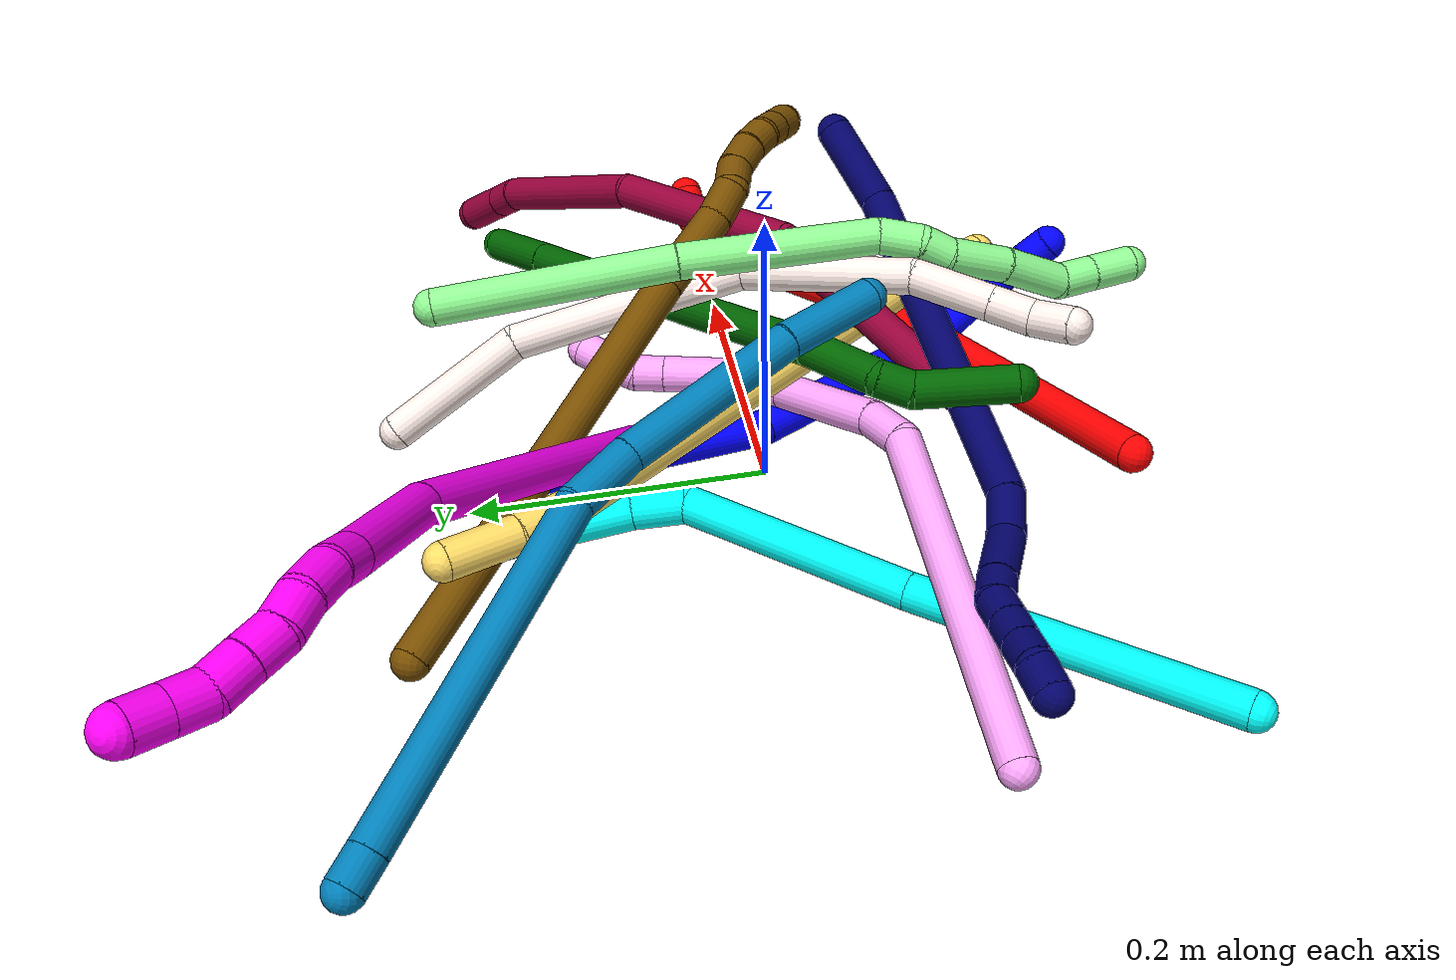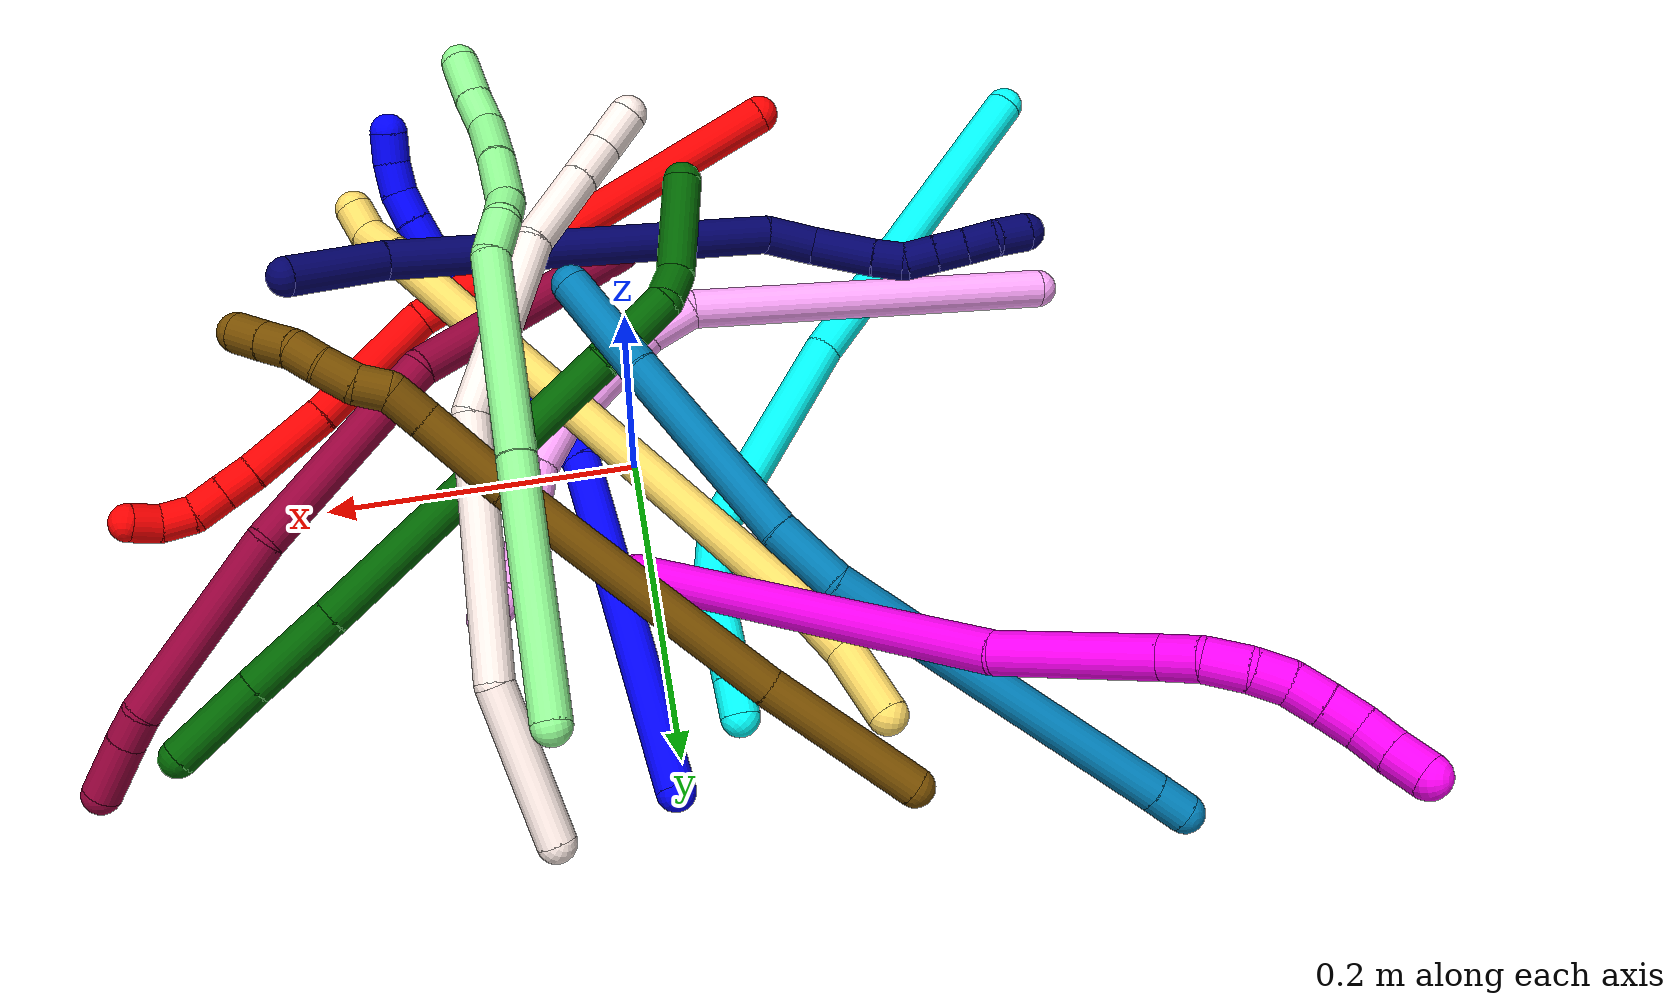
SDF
<sdf version="1.7">
 <world name="default">
  <plugin name="TubeGeneratorPlugin" filename="libtube_generator_plugin.so"/>
  <model name="photoneo_s_sensor">
   <static>1</static>
   <pose>0 0 2 1.57079 1.57079 3.14159</pose>
   <link name="link">
    <inertial><mass>0.1</mass></inertial>
    <sensor name="sensor" type="depth">
     <update_rate>30</update_rate>
     <camera>
      <horizontal_fov>1.22</horizontal_fov>
      <image><width>1920</width><height>1200</height><format>B8G8R8</format></image>
      <clip><near>0.1</near><far>4</far></clip>
      <depth_camera><output>points</output></depth_camera>
     </camera>
     <plugin name="camera_plugin" filename="libgazebo_ros_depth_camera.so">
      <baseline>0.2</baseline>
      <alwaysOn>1</alwaysOn>
      <updateRate>0.0</updateRate>
      <cameraName>camera_ir</cameraName>
      <imageTopicName>/camera/color/image_raw</imageTopicName>
      <cameraInfoTopicName>/camera/color/camera_info</cameraInfoTopicName>
      <depthImageTopicName>/camera/depth/image_raw</depthImageTopicName>
      <depthImageCameraInfoTopicName>/camera/depth/camera_info</depthImageCameraInfoTopicName>
      <pointCloudTopicName>/camera/depth/points</pointCloudTopicName>
      <frameName>fr_optical</frameName>
      <pointCloudCutoff>0.1</pointCloudCutoff>
      <pointCloudCutoffMax>2.0</pointCloudCutoffMax>
      <distortionK1>0</distortionK1>
      <distortionK2>0</distortionK2>
      <distortionK3>0</distortionK3>
      <distortionT1>0</distortionT1>
      <distortionT2>0</distortionT2>
      <CxPrime>0</CxPrime>
      <Cx>0</Cx>
      <Cy>0</Cy>
      <focalLength>0</focalLength>
      <hackBaseline>0</hackBaseline>
     </plugin>
    </sensor>
   </link>
  </model>
  <gravity>0 0 -9.8</gravity>
  <magnetic_field>6e-06 2.3e-05 -4.2e-05</magnetic_field>
  <atmosphere type="adiabatic"/>
  <physics name="default_physics" default="0" type="ode">
   <max_step_size>0.003</max_step_size>
   <real_time_factor>1</real_time_factor>
   <real_time_update_rate>1000</real_time_update_rate>
   <max_contacts>10000</max_contacts>
   <ode>
    <solver>
     <type>quick</type>
     <iters>100</iters>
     <sor>1.3</sor>
     <use_dynamic_moi_rescaling>0</use_dynamic_moi_rescaling>
    </solver>
    <constraints>
     <contact_max_correcting_vel>0</contact_max_correcting_vel>
     <contact_surface_layer>0.001</contact_surface_layer>
     <cfm>0</cfm>
     <erp>0.2</erp>
    </constraints>
   </ode>
  </physics>
  <scene><ambient>0.4 0.4 0.4 1</ambient><background>0.7 0.7 0.7 1</background><shadows>0</shadows></scene>
  <audio><device>default</device></audio>
  <spherical_coordinates>
   <surface_model>EARTH_WGS84</surface_model>
   <latitude_deg>0</latitude_deg>
   <longitude_deg>0</longitude_deg>
   <elevation>0</elevation>
   <heading_deg>0</heading_deg>
  </spherical_coordinates>
  <model name="bin">
   <static>1</static>
   <link name="bottom">
    <collision name="collision-bottom">
     <pose>0 0 -0.01 0 -0 0</pose>
     <geometry><box><size>0.8 0.6 0.02</size></box></geometry>
     <surface>
      <friction><ode><mu>100</mu><mu2>100</mu2></ode></friction>
      <contact><collide_bitmask>65535</collide_bitmask></contact>
     </surface>
    </collision>
   </link>
   <link name="west_wall">
    <collision name="collision-west_wall">
     <pose>-0.41 0 0.1 0 -0 0</pose>
     <geometry><box><size>0.02 0.6 0.2</size></box></geometry>
     <surface>
      <friction><ode><mu>100</mu><mu2>100</mu2></ode></friction>
      <contact><collide_bitmask>65535</collide_bitmask></contact>
     </surface>
    </collision>
   </link>
   <link name="east_wall">
    <collision name="collision-east_wall">
     <pose>0.41 0 0.1 0 -0 0</pose>
     <geometry><box><size>0.02 0.6 0.2</size></box></geometry>
     <surface>
      <friction><ode><mu>100</mu><mu2>100</mu2></ode></friction>
      <contact><collide_bitmask>65535</collide_bitmask></contact>
     </surface>
    </collision>
   </link>
   <link name="south_wall">
    <collision name="collision-south_wall">
     <pose>0 -0.31 0.1 0 -0 0</pose>
     <geometry><box><size>0.8 0.02 0.2</size></box></geometry>
     <surface>
      <friction><ode><mu>100</mu><mu2>100</mu2></ode></friction>
      <contact><collide_bitmask>65535</collide_bitmask></contact>
     </surface>
    </collision>
   </link>
   <link name="north_wall">
    <collision name="collision-north_wall">
     <pose>0 0.31 0.1 0 -0 0</pose>
     <geometry><box><size>0.8 0.02 0.2</size></box></geometry>
     <surface>
      <friction><ode><mu>100</mu><mu2>100</mu2></ode></friction>
      <contact><collide_bitmask>65535</collide_bitmask></contact>
     </surface>
    </collision>
   </link>
  </model>
  <model name="1">
   <static>0</static>
   <link name="1">
    <collision name="collision-cylinder-e_1_1_4">
     <pose>0.021706 -0.098961 -0.053769 2.06851 0.190398 0.318391</pose>
     <geometry><cylinder><radius>0.0125</radius><length>0.229395</length></cylinder></geometry>
     <surface>
      <friction><ode><mu>1.16</mu><mu2>1.16</mu2><slip1>0</slip1><slip2>0</slip2></ode></friction>
      <contact><ode><kp>1e+06</kp><kd>1</kd><max_vel>0</max_vel><min_depth>0.001</min_depth></ode></contact>
     </surface>
    </collision>
    <visual name="visual-cylinder-e_1_1_4">
     <pose>0.021706 -0.098961 -0.053769 2.06851 0.190398 0.318391</pose>
     <geometry><cylinder><radius>0.0125</radius><length>0.229395</length></cylinder></geometry>
     <material><ambient>0 0 1 1</ambient></material>
    </visual>
    <collision name="collision-cylinder-e_2_4_5">
     <pose>0.073482 -0.240779 -0.140738 2.2299 0.506398 0.971214</pose>
     <geometry><cylinder><radius>0.0125</radius><length>0.123987</length></cylinder></geometry>
     <surface>
      <friction><ode><mu>1.16</mu><mu2>1.16</mu2><slip1>0</slip1><slip2>0</slip2></ode></friction>
      <contact><ode><kp>1e+06</kp><kd>1</kd><max_vel>0</max_vel><min_depth>0.001</min_depth></ode></contact>
     </surface>
    </collision>
    <visual name="visual-cylinder-e_2_4_5">
     <pose>0.073482 -0.240779 -0.140738 2.2299 0.506398 0.971214</pose>
     <geometry><cylinder><radius>0.0125</radius><length>0.123987</length></cylinder></geometry>
     <material><ambient>0 0 1 1</ambient></material>
    </visual>
    <collision name="collision-cylinder-e_3_5_6">
     <pose>0.108422 -0.291187 -0.179608 2.2148 0.476355 0.904568</pose>
     <geometry><cylinder><radius>0.0125</radius><length>0.02125</length></cylinder></geometry>
     <surface>
      <friction><ode><mu>1.16</mu><mu2>1.16</mu2><slip1>0</slip1><slip2>0</slip2></ode></friction>
      <contact><ode><kp>1e+06</kp><kd>1</kd><max_vel>0</max_vel><min_depth>0.001</min_depth></ode></contact>
     </surface>
    </collision>
    <visual name="visual-cylinder-e_3_5_6">
     <pose>0.108422 -0.291187 -0.179608 2.2148 0.476355 0.904568</pose>
     <geometry><cylinder><radius>0.0125</radius><length>0.02125</length></cylinder></geometry>
     <material><ambient>0 0 1 1</ambient></material>
    </visual>
    <collision name="collision-cylinder-e_4_6_7">
     <pose>0.131055 -0.324 -0.189454 1.73467 0.606442 0.706743</pose>
     <geometry><cylinder><radius>0.0125</radius><length>0.062323</length></cylinder></geometry>
     <surface>
      <friction><ode><mu>1.16</mu><mu2>1.16</mu2><slip1>0</slip1><slip2>0</slip2></ode></friction>
      <contact><ode><kp>1e+06</kp><kd>1</kd><max_vel>0</max_vel><min_depth>0.001</min_depth></ode></contact>
     </surface>
    </collision>
    <visual name="visual-cylinder-e_4_6_7">
     <pose>0.131055 -0.324 -0.189454 1.73467 0.606442 0.706743</pose>
     <geometry><cylinder><radius>0.0125</radius><length>0.062323</length></cylinder></geometry>
     <material><ambient>0 0 1 1</ambient></material>
    </visual>
    <collision name="collision-cylinder-e_5_7_8">
     <pose>0.154404 -0.358281 -0.195299 1.75358 0.547292 0.650682</pose>
     <geometry><cylinder><radius>0.0125</radius><length>0.02148</length></cylinder></geometry>
     <surface>
      <friction><ode><mu>1.16</mu><mu2>1.16</mu2><slip1>0</slip1><slip2>0</slip2></ode></friction>
      <contact><ode><kp>1e+06</kp><kd>1</kd><max_vel>0</max_vel><min_depth>0.001</min_depth></ode></contact>
     </surface>
    </collision>
    <visual name="visual-cylinder-e_5_7_8">
     <pose>0.154404 -0.358281 -0.195299 1.75358 0.547292 0.650682</pose>
     <geometry><cylinder><radius>0.0125</radius><length>0.02148</length></cylinder></geometry>
     <material><ambient>0 0 1 1</ambient></material>
    </visual>
    <collision name="collision-cylinder-e_6_8_9">
     <pose>0.163837 -0.377123 -0.196487 1.52211 0.372592 0.355258</pose>
     <geometry><cylinder><radius>0.0125</radius><length>0.02112</length></cylinder></geometry>
     <surface>
      <friction><ode><mu>1.16</mu><mu2>1.16</mu2><slip1>0</slip1><slip2>0</slip2></ode></friction>
      <contact><ode><kp>1e+06</kp><kd>1</kd><max_vel>0</max_vel><min_depth>0.001</min_depth></ode></contact>
     </surface>
    </collision>
    <visual name="visual-cylinder-e_6_8_9">
     <pose>0.163837 -0.377123 -0.196487 1.52211 0.372592 0.355258</pose>
     <geometry><cylinder><radius>0.0125</radius><length>0.02112</length></cylinder></geometry>
     <material><ambient>0 0 1 1</ambient></material>
    </visual>
    <collision name="collision-cylinder-e_7_9_2">
     <pose>0.170445 -0.396523 -0.193737 1.3379 0.273707 0.216884</pose>
     <geometry><cylinder><radius>0.0125</radius><length>0.020445</length></cylinder></geometry>
     <surface>
      <friction><ode><mu>1.16</mu><mu2>1.16</mu2><slip1>0</slip1><slip2>0</slip2></ode></friction>
      <contact><ode><kp>1e+06</kp><kd>1</kd><max_vel>0</max_vel><min_depth>0.001</min_depth></ode></contact>
     </surface>
    </collision>
    <visual name="visual-cylinder-e_7_9_2">
     <pose>0.170445 -0.396523 -0.193737 1.3379 0.273707 0.216884</pose>
     <geometry><cylinder><radius>0.0125</radius><length>0.020445</length></cylinder></geometry>
     <material><ambient>0 0 1 1</ambient></material>
    </visual>
    <collision name="collision-sphere-2">
     <pose>0.173208 -0.406099 -0.191466 0 -0 0</pose>
     <geometry><sphere><radius>0.0125</radius></sphere></geometry>
     <surface>
      <friction><ode><mu>1.16</mu><mu2>1.16</mu2><slip1>0</slip1><slip2>0</slip2></ode></friction>
      <contact><ode><kp>1e+06</kp><kd>1</kd><max_vel>0</max_vel><min_depth>0.001</min_depth></ode></contact>
     </surface>
    </collision>
    <visual name="visual-sphere-2">
     <pose>0.173208 -0.406099 -0.191466 0 -0 0</pose>
     <geometry><sphere><radius>0.0125</radius></sphere></geometry>
     <material><ambient>0 0 1 1</ambient></material>
    </visual>
    <collision name="collision-sphere-9">
     <pose>0.167682 -0.386947 -0.196009 0 -0 0</pose>
     <geometry><sphere><radius>0.0125</radius></sphere></geometry>
     <surface>
      <friction><ode><mu>1.16</mu><mu2>1.16</mu2><slip1>0</slip1><slip2>0</slip2></ode></friction>
      <contact><ode><kp>1e+06</kp><kd>1</kd><max_vel>0</max_vel><min_depth>0.001</min_depth></ode></contact>
     </surface>
    </collision>
    <visual name="visual-sphere-9">
     <pose>0.167682 -0.386947 -0.196009 0 -0 0</pose>
     <geometry><sphere><radius>0.0125</radius></sphere></geometry>
     <material><ambient>0 0 1 1</ambient></material>
    </visual>
    <collision name="collision-sphere-4">
     <pose>0.043413 -0.197921 -0.107538 0 -0 0</pose>
     <geometry><sphere><radius>0.0125</radius></sphere></geometry>
     <surface>
      <friction><ode><mu>1.16</mu><mu2>1.16</mu2><slip1>0</slip1><slip2>0</slip2></ode></friction>
      <contact><ode><kp>1e+06</kp><kd>1</kd><max_vel>0</max_vel><min_depth>0.001</min_depth></ode></contact>
     </surface>
    </collision>
    <visual name="visual-sphere-4">
     <pose>0.043413 -0.197921 -0.107538 0 -0 0</pose>
     <geometry><sphere><radius>0.0125</radius></sphere></geometry>
     <material><ambient>0 0 1 1</ambient></material>
    </visual>
    <collision name="collision-sphere-1">
     <geometry><sphere><radius>0.0125</radius></sphere></geometry>
     <surface>
      <friction><ode><mu>1.16</mu><mu2>1.16</mu2><slip1>0</slip1><slip2>0</slip2></ode></friction>
      <contact><ode><kp>1e+06</kp><kd>1</kd><max_vel>0</max_vel><min_depth>0.001</min_depth></ode></contact>
     </surface>
    </collision>
    <visual name="visual-sphere-1">
     <geometry><sphere><radius>0.0125</radius></sphere></geometry>
     <material><ambient>0 0 1 1</ambient></material>
    </visual>
    <collision name="collision-sphere-8">
     <pose>0.159993 -0.367299 -0.196966 0 -0 0</pose>
     <geometry><sphere><radius>0.0125</radius></sphere></geometry>
     <surface>
      <friction><ode><mu>1.16</mu><mu2>1.16</mu2><slip1>0</slip1><slip2>0</slip2></ode></friction>
      <contact><ode><kp>1e+06</kp><kd>1</kd><max_vel>0</max_vel><min_depth>0.001</min_depth></ode></contact>
     </surface>
    </collision>
    <visual name="visual-sphere-8">
     <pose>0.159993 -0.367299 -0.196966 0 -0 0</pose>
     <geometry><sphere><radius>0.0125</radius></sphere></geometry>
     <material><ambient>0 0 1 1</ambient></material>
    </visual>
    <collision name="collision-sphere-5">
     <pose>0.10355 -0.283636 -0.173939 0 -0 0</pose>
     <geometry><sphere><radius>0.0125</radius></sphere></geometry>
     <surface>
      <friction><ode><mu>1.16</mu><mu2>1.16</mu2><slip1>0</slip1><slip2>0</slip2></ode></friction>
      <contact><ode><kp>1e+06</kp><kd>1</kd><max_vel>0</max_vel><min_depth>0.001</min_depth></ode></contact>
     </surface>
    </collision>
    <visual name="visual-sphere-5">
     <pose>0.10355 -0.283636 -0.173939 0 -0 0</pose>
     <geometry><sphere><radius>0.0125</radius></sphere></geometry>
     <material><ambient>0 0 1 1</ambient></material>
    </visual>
    <collision name="collision-sphere-6">
     <pose>0.113294 -0.298738 -0.185277 0 -0 0</pose>
     <geometry><sphere><radius>0.0125</radius></sphere></geometry>
     <surface>
      <friction><ode><mu>1.16</mu><mu2>1.16</mu2><slip1>0</slip1><slip2>0</slip2></ode></friction>
      <contact><ode><kp>1e+06</kp><kd>1</kd><max_vel>0</max_vel><min_depth>0.001</min_depth></ode></contact>
     </surface>
    </collision>
    <visual name="visual-sphere-6">
     <pose>0.113294 -0.298738 -0.185277 0 -0 0</pose>
     <geometry><sphere><radius>0.0125</radius></sphere></geometry>
     <material><ambient>0 0 1 1</ambient></material>
    </visual>
    <collision name="collision-sphere-7">
     <pose>0.148815 -0.349262 -0.193632 0 -0 0</pose>
     <geometry><sphere><radius>0.0125</radius></sphere></geometry>
     <surface>
      <friction><ode><mu>1.16</mu><mu2>1.16</mu2><slip1>0</slip1><slip2>0</slip2></ode></friction>
      <contact><ode><kp>1e+06</kp><kd>1</kd><max_vel>0</max_vel><min_depth>0.001</min_depth></ode></contact>
     </surface>
    </collision>
    <visual name="visual-sphere-7">
     <pose>0.148815 -0.349262 -0.193632 0 -0 0</pose>
     <geometry><sphere><radius>0.0125</radius></sphere></geometry>
     <material><ambient>0 0 1 1</ambient></material>
    </visual>
    <inertial>
     <pose>0.069647 -0.205405 -0.115428 0 -0 0</pose>
     <mass>0.5</mass>
     <inertia><ixx>0.001505</ixx><ixy>0</ixy><ixz>0</ixz><iyy>7e-06</iyy><iyz>0</iyz><izz>0.000711</izz></inertia>
    </inertial>
   </link>
   <pose>0.006772 0.222565 0.010887 -0.415862 -0.412497 -0.088913</pose>
  </model>
  <model name="2">
   <static>0</static>
   <link name="2">
    <collision name="collision-cylinder-e_1_1_4">
     <pose>0.065254 0.098574 -0.057438 -2.09839 0.519549 -0.866362</pose>
     <geometry><cylinder><radius>0.0125</radius><length>0.262861</length></cylinder></geometry>
     <surface>
      <friction><ode><mu>1.16</mu><mu2>1.16</mu2><slip1>0</slip1><slip2>0</slip2></ode></friction>
      <contact><ode><kp>1e+06</kp><kd>1</kd><max_vel>0</max_vel><min_depth>0.001</min_depth></ode></contact>
     </surface>
    </collision>
    <visual name="visual-cylinder-e_1_1_4">
     <pose>0.065254 0.098574 -0.057438 -2.09839 0.519549 -0.866362</pose>
     <geometry><cylinder><radius>0.0125</radius><length>0.262861</length></cylinder></geometry>
     <material><ambient>1 0 0 1</ambient></material>
    </visual>
    <collision name="collision-cylinder-e_2_4_5">
     <pose>0.148873 0.224107 -0.147189 -2.44626 0.411507 -1.04506</pose>
     <geometry><cylinder><radius>0.0125</radius><length>0.091833</length></cylinder></geometry>
     <surface>
      <friction><ode><mu>1.16</mu><mu2>1.16</mu2><slip1>0</slip1><slip2>0</slip2></ode></friction>
      <contact><ode><kp>1e+06</kp><kd>1</kd><max_vel>0</max_vel><min_depth>0.001</min_depth></ode></contact>
     </surface>
    </collision>
    <visual name="visual-cylinder-e_2_4_5">
     <pose>0.148873 0.224107 -0.147189 -2.44626 0.411507 -1.04506</pose>
     <geometry><cylinder><radius>0.0125</radius><length>0.091833</length></cylinder></geometry>
     <material><ambient>1 0 0 1</ambient></material>
    </visual>
    <collision name="collision-cylinder-e_3_5_6">
     <pose>0.179117 0.269653 -0.197678 -2.34503 0.428594 -0.954695</pose>
     <geometry><cylinder><radius>0.0125</radius><length>0.057162</length></cylinder></geometry>
     <surface>
      <friction><ode><mu>1.16</mu><mu2>1.16</mu2><slip1>0</slip1><slip2>0</slip2></ode></friction>
      <contact><ode><kp>1e+06</kp><kd>1</kd><max_vel>0</max_vel><min_depth>0.001</min_depth></ode></contact>
     </surface>
    </collision>
    <visual name="visual-cylinder-e_3_5_6">
     <pose>0.179117 0.269653 -0.197678 -2.34503 0.428594 -0.954695</pose>
     <geometry><cylinder><radius>0.0125</radius><length>0.057162</length></cylinder></geometry>
     <material><ambient>1 0 0 1</ambient></material>
    </visual>
    <collision name="collision-cylinder-e_4_6_7">
     <pose>0.195397 0.296234 -0.222456 -2.26111 0.401475 -0.815474</pose>
     <geometry><cylinder><radius>0.0125</radius><length>0.02253</length></cylinder></geometry>
     <surface>
      <friction><ode><mu>1.16</mu><mu2>1.16</mu2><slip1>0</slip1><slip2>0</slip2></ode></friction>
      <contact><ode><kp>1e+06</kp><kd>1</kd><max_vel>0</max_vel><min_depth>0.001</min_depth></ode></contact>
     </surface>
    </collision>
    <visual name="visual-cylinder-e_4_6_7">
     <pose>0.195397 0.296234 -0.222456 -2.26111 0.401475 -0.815474</pose>
     <geometry><cylinder><radius>0.0125</radius><length>0.02253</length></cylinder></geometry>
     <material><ambient>1 0 0 1</ambient></material>
    </visual>
    <collision name="collision-cylinder-e_5_7_8">
     <pose>0.204205 0.312219 -0.235958 -2.28309 0.395393 -0.825046</pose>
     <geometry><cylinder><radius>0.0125</radius><length>0.022878</length></cylinder></geometry>
     <surface>
      <friction><ode><mu>1.16</mu><mu2>1.16</mu2><slip1>0</slip1><slip2>0</slip2></ode></friction>
      <contact><ode><kp>1e+06</kp><kd>1</kd><max_vel>0</max_vel><min_depth>0.001</min_depth></ode></contact>
     </surface>
    </collision>
    <visual name="visual-cylinder-e_5_7_8">
     <pose>0.204205 0.312219 -0.235958 -2.28309 0.395393 -0.825046</pose>
     <geometry><cylinder><radius>0.0125</radius><length>0.022878</length></cylinder></geometry>
     <material><ambient>1 0 0 1</ambient></material>
    </visual>
    <collision name="collision-cylinder-e_6_8_9">
     <pose>0.211013 0.330186 -0.246814 -1.9483 0.220173 -0.322641</pose>
     <geometry><cylinder><radius>0.0125</radius><length>0.021998</length></cylinder></geometry>
     <surface>
      <friction><ode><mu>1.16</mu><mu2>1.16</mu2><slip1>0</slip1><slip2>0</slip2></ode></friction>
      <contact><ode><kp>1e+06</kp><kd>1</kd><max_vel>0</max_vel><min_depth>0.001</min_depth></ode></contact>
     </surface>
    </collision>
    <visual name="visual-cylinder-e_6_8_9">
     <pose>0.211013 0.330186 -0.246814 -1.9483 0.220173 -0.322641</pose>
     <geometry><cylinder><radius>0.0125</radius><length>0.021998</length></cylinder></geometry>
     <material><ambient>1 0 0 1</ambient></material>
    </visual>
    <collision name="collision-cylinder-e_7_9_2">
     <pose>0.211063 0.349819 -0.253734 -1.8686 -0.228797 0.308446</pose>
     <geometry><cylinder><radius>0.0125</radius><length>0.02074</length></cylinder></geometry>
     <surface>
      <friction><ode><mu>1.16</mu><mu2>1.16</mu2><slip1>0</slip1><slip2>0</slip2></ode></friction>
      <contact><ode><kp>1e+06</kp><kd>1</kd><max_vel>0</max_vel><min_depth>0.001</min_depth></ode></contact>
     </surface>
    </collision>
    <visual name="visual-cylinder-e_7_9_2">
     <pose>0.211063 0.349819 -0.253734 -1.8686 -0.228797 0.308446</pose>
     <geometry><cylinder><radius>0.0125</radius><length>0.02074</length></cylinder></geometry>
     <material><ambient>1 0 0 1</ambient></material>
    </visual>
    <collision name="collision-sphere-2">
     <pose>0.208711 0.359474 -0.256697 0 -0 0</pose>
     <geometry><sphere><radius>0.0125</radius></sphere></geometry>
     <surface>
      <friction><ode><mu>1.16</mu><mu2>1.16</mu2><slip1>0</slip1><slip2>0</slip2></ode></friction>
      <contact><ode><kp>1e+06</kp><kd>1</kd><max_vel>0</max_vel><min_depth>0.001</min_depth></ode></contact>
     </surface>
    </collision>
    <visual name="visual-sphere-2">
     <pose>0.208711 0.359474 -0.256697 0 -0 0</pose>
     <geometry><sphere><radius>0.0125</radius></sphere></geometry>
     <material><ambient>1 0 0 1</ambient></material>
    </visual>
    <collision name="collision-sphere-9">
     <pose>0.213415 0.340163 -0.25077 0 -0 0</pose>
     <geometry><sphere><radius>0.0125</radius></sphere></geometry>
     <surface>
      <friction><ode><mu>1.16</mu><mu2>1.16</mu2><slip1>0</slip1><slip2>0</slip2></ode></friction>
      <contact><ode><kp>1e+06</kp><kd>1</kd><max_vel>0</max_vel><min_depth>0.001</min_depth></ode></contact>
     </surface>
    </collision>
    <visual name="visual-sphere-9">
     <pose>0.213415 0.340163 -0.25077 0 -0 0</pose>
     <geometry><sphere><radius>0.0125</radius></sphere></geometry>
     <material><ambient>1 0 0 1</ambient></material>
    </visual>
    <collision name="collision-sphere-4">
     <pose>0.130507 0.197147 -0.114876 0 -0 0</pose>
     <geometry><sphere><radius>0.0125</radius></sphere></geometry>
     <surface>
      <friction><ode><mu>1.16</mu><mu2>1.16</mu2><slip1>0</slip1><slip2>0</slip2></ode></friction>
      <contact><ode><kp>1e+06</kp><kd>1</kd><max_vel>0</max_vel><min_depth>0.001</min_depth></ode></contact>
     </surface>
    </collision>
    <visual name="visual-sphere-4">
     <pose>0.130507 0.197147 -0.114876 0 -0 0</pose>
     <geometry><sphere><radius>0.0125</radius></sphere></geometry>
     <material><ambient>1 0 0 1</ambient></material>
    </visual>
    <collision name="collision-sphere-1">
     <geometry><sphere><radius>0.0125</radius></sphere></geometry>
     <surface>
      <friction><ode><mu>1.16</mu><mu2>1.16</mu2><slip1>0</slip1><slip2>0</slip2></ode></friction>
      <contact><ode><kp>1e+06</kp><kd>1</kd><max_vel>0</max_vel><min_depth>0.001</min_depth></ode></contact>
     </surface>
    </collision>
    <visual name="visual-sphere-1">
     <geometry><sphere><radius>0.0125</radius></sphere></geometry>
     <material><ambient>1 0 0 1</ambient></material>
    </visual>
    <collision name="collision-sphere-8">
     <pose>0.208611 0.320208 -0.242858 0 -0 0</pose>
     <geometry><sphere><radius>0.0125</radius></sphere></geometry>
     <surface>
      <friction><ode><mu>1.16</mu><mu2>1.16</mu2><slip1>0</slip1><slip2>0</slip2></ode></friction>
      <contact><ode><kp>1e+06</kp><kd>1</kd><max_vel>0</max_vel><min_depth>0.001</min_depth></ode></contact>
     </surface>
    </collision>
    <visual name="visual-sphere-8">
     <pose>0.208611 0.320208 -0.242858 0 -0 0</pose>
     <geometry><sphere><radius>0.0125</radius></sphere></geometry>
     <material><ambient>1 0 0 1</ambient></material>
    </visual>
    <collision name="collision-sphere-5">
     <pose>0.167239 0.251067 -0.179503 0 -0 0</pose>
     <geometry><sphere><radius>0.0125</radius></sphere></geometry>
     <surface>
      <friction><ode><mu>1.16</mu><mu2>1.16</mu2><slip1>0</slip1><slip2>0</slip2></ode></friction>
      <contact><ode><kp>1e+06</kp><kd>1</kd><max_vel>0</max_vel><min_depth>0.001</min_depth></ode></contact>
     </surface>
    </collision>
    <visual name="visual-sphere-5">
     <pose>0.167239 0.251067 -0.179503 0 -0 0</pose>
     <geometry><sphere><radius>0.0125</radius></sphere></geometry>
     <material><ambient>1 0 0 1</ambient></material>
    </visual>
    <collision name="collision-sphere-6">
     <pose>0.190995 0.288239 -0.215854 0 -0 0</pose>
     <geometry><sphere><radius>0.0125</radius></sphere></geometry>
     <surface>
      <friction><ode><mu>1.16</mu><mu2>1.16</mu2><slip1>0</slip1><slip2>0</slip2></ode></friction>
      <contact><ode><kp>1e+06</kp><kd>1</kd><max_vel>0</max_vel><min_depth>0.001</min_depth></ode></contact>
     </surface>
    </collision>
    <visual name="visual-sphere-6">
     <pose>0.190995 0.288239 -0.215854 0 -0 0</pose>
     <geometry><sphere><radius>0.0125</radius></sphere></geometry>
     <material><ambient>1 0 0 1</ambient></material>
    </visual>
    <collision name="collision-sphere-7">
     <pose>0.199799 0.304229 -0.229059 0 -0 0</pose>
     <geometry><sphere><radius>0.0125</radius></sphere></geometry>
     <surface>
      <friction><ode><mu>1.16</mu><mu2>1.16</mu2><slip1>0</slip1><slip2>0</slip2></ode></friction>
      <contact><ode><kp>1e+06</kp><kd>1</kd><max_vel>0</max_vel><min_depth>0.001</min_depth></ode></contact>
     </surface>
    </collision>
    <visual name="visual-sphere-7">
     <pose>0.199799 0.304229 -0.229059 0 -0 0</pose>
     <geometry><sphere><radius>0.0125</radius></sphere></geometry>
     <material><ambient>1 0 0 1</ambient></material>
    </visual>
    <inertial>
     <pose>0.118312 0.180482 -0.122033 0 -0 0</pose>
     <mass>0.5</mass>
     <inertia>
      <ixx>-0.000159</ixx>
      <ixy>0</ixy>
      <ixz>0</ixz>
      <iyy>-0.001064</iyy>
      <iyz>0</iyz>
      <izz>-0.002013</izz>
     </inertia>
    </inertial>
   </link>
   <pose>-0.116721 -0.208303 0.078136 2.24653 1.23374 0.493743</pose>
  </model>
  <model name="3">
   <static>0</static>
   <link name="3">
    <collision name="collision-cylinder-e_1_1_4">
     <pose>-0.010333 0.005504 -0.11041 -3.09178 -0.093197 2.16032</pose>
     <geometry><cylinder><radius>0.0125</radius><length>0.222058</length></cylinder></geometry>
     <surface>
      <friction><ode><mu>1.16</mu><mu2>1.16</mu2><slip1>0</slip1><slip2>0</slip2></ode></friction>
      <contact><ode><kp>1e+06</kp><kd>1</kd><max_vel>0</max_vel><min_depth>0.001</min_depth></ode></contact>
     </surface>
    </collision>
    <visual name="visual-cylinder-e_1_1_4">
     <pose>-0.010333 0.005504 -0.11041 -3.09178 -0.093197 2.16032</pose>
     <geometry><cylinder><radius>0.0125</radius><length>0.222058</length></cylinder></geometry>
     <material><ambient>0.003922 1 0.996078 1</ambient></material>
    </visual>
    <collision name="collision-cylinder-e_2_4_5">
     <pose>-0.00787 0.016282 -0.297161 -3.07263 0.165671 -2.35402</pose>
     <geometry><cylinder><radius>0.0125</radius><length>0.155169</length></cylinder></geometry>
     <surface>
      <friction><ode><mu>1.16</mu><mu2>1.16</mu2><slip1>0</slip1><slip2>0</slip2></ode></friction>
      <contact><ode><kp>1e+06</kp><kd>1</kd><max_vel>0</max_vel><min_depth>0.001</min_depth></ode></contact>
     </surface>
    </collision>
    <visual name="visual-cylinder-e_2_4_5">
     <pose>-0.00787 0.016282 -0.297161 -3.07263 0.165671 -2.35402</pose>
     <geometry><cylinder><radius>0.0125</radius><length>0.155169</length></cylinder></geometry>
     <material><ambient>0.003922 1 0.996078 1</ambient></material>
    </visual>
    <collision name="collision-cylinder-e_3_5_6">
     <pose>0.006607 0.031139 -0.388984 -2.5873 0.092164 -0.321422</pose>
     <geometry><cylinder><radius>0.0125</radius><length>0.036575</length></cylinder></geometry>
     <surface>
      <friction><ode><mu>1.16</mu><mu2>1.16</mu2><slip1>0</slip1><slip2>0</slip2></ode></friction>
      <contact><ode><kp>1e+06</kp><kd>1</kd><max_vel>0</max_vel><min_depth>0.001</min_depth></ode></contact>
     </surface>
    </collision>
    <visual name="visual-cylinder-e_3_5_6">
     <pose>0.006607 0.031139 -0.388984 -2.5873 0.092164 -0.321422</pose>
     <geometry><cylinder><radius>0.0125</radius><length>0.036575</length></cylinder></geometry>
     <material><ambient>0.003922 1 0.996078 1</ambient></material>
    </visual>
    <collision name="collision-cylinder-e_4_6_7">
     <pose>0.017482 0.061595 -0.425555 -2.36135 0.300431 -0.70539</pose>
     <geometry><cylinder><radius>0.0125</radius><length>0.062121</length></cylinder></geometry>
     <surface>
      <friction><ode><mu>1.16</mu><mu2>1.16</mu2><slip1>0</slip1><slip2>0</slip2></ode></friction>
      <contact><ode><kp>1e+06</kp><kd>1</kd><max_vel>0</max_vel><min_depth>0.001</min_depth></ode></contact>
     </surface>
    </collision>
    <visual name="visual-cylinder-e_4_6_7">
     <pose>0.017482 0.061595 -0.425555 -2.36135 0.300431 -0.70539</pose>
     <geometry><cylinder><radius>0.0125</radius><length>0.062121</length></cylinder></geometry>
     <material><ambient>0.003922 1 0.996078 1</ambient></material>
    </visual>
    <collision name="collision-cylinder-e_5_7_2">
     <pose>0.030039 0.090591 -0.454863 -2.36202 0.283255 -0.668143</pose>
     <geometry><cylinder><radius>0.0125</radius><length>0.024077</length></cylinder></geometry>
     <surface>
      <friction><ode><mu>1.16</mu><mu2>1.16</mu2><slip1>0</slip1><slip2>0</slip2></ode></friction>
      <contact><ode><kp>1e+06</kp><kd>1</kd><max_vel>0</max_vel><min_depth>0.001</min_depth></ode></contact>
     </surface>
    </collision>
    <visual name="visual-cylinder-e_5_7_2">
     <pose>0.030039 0.090591 -0.454863 -2.36202 0.283255 -0.668143</pose>
     <geometry><cylinder><radius>0.0125</radius><length>0.024077</length></cylinder></geometry>
     <material><ambient>0.003922 1 0.996078 1</ambient></material>
    </visual>
    <collision name="collision-sphere-2">
     <pose>0.033403 0.098717 -0.463084 0 -0 0</pose>
     <geometry><sphere><radius>0.0125</radius></sphere></geometry>
     <surface>
      <friction><ode><mu>1.16</mu><mu2>1.16</mu2><slip1>0</slip1><slip2>0</slip2></ode></friction>
      <contact><ode><kp>1e+06</kp><kd>1</kd><max_vel>0</max_vel><min_depth>0.001</min_depth></ode></contact>
     </surface>
    </collision>
    <visual name="visual-sphere-2">
     <pose>0.033403 0.098717 -0.463084 0 -0 0</pose>
     <geometry><sphere><radius>0.0125</radius></sphere></geometry>
     <material><ambient>0.003922 1 0.996078 1</ambient></material>
    </visual>
    <collision name="collision-sphere-7">
     <pose>0.026674 0.082466 -0.446642 0 -0 0</pose>
     <geometry><sphere><radius>0.0125</radius></sphere></geometry>
     <surface>
      <friction><ode><mu>1.16</mu><mu2>1.16</mu2><slip1>0</slip1><slip2>0</slip2></ode></friction>
      <contact><ode><kp>1e+06</kp><kd>1</kd><max_vel>0</max_vel><min_depth>0.001</min_depth></ode></contact>
     </surface>
    </collision>
    <visual name="visual-sphere-7">
     <pose>0.026674 0.082466 -0.446642 0 -0 0</pose>
     <geometry><sphere><radius>0.0125</radius></sphere></geometry>
     <material><ambient>0.003922 1 0.996078 1</ambient></material>
    </visual>
    <collision name="collision-sphere-6">
     <pose>0.008291 0.040724 -0.404468 0 -0 0</pose>
     <geometry><sphere><radius>0.0125</radius></sphere></geometry>
     <surface>
      <friction><ode><mu>1.16</mu><mu2>1.16</mu2><slip1>0</slip1><slip2>0</slip2></ode></friction>
      <contact><ode><kp>1e+06</kp><kd>1</kd><max_vel>0</max_vel><min_depth>0.001</min_depth></ode></contact>
     </surface>
    </collision>
    <visual name="visual-sphere-6">
     <pose>0.008291 0.040724 -0.404468 0 -0 0</pose>
     <geometry><sphere><radius>0.0125</radius></sphere></geometry>
     <material><ambient>0.003922 1 0.996078 1</ambient></material>
    </visual>
    <collision name="collision-sphere-5">
     <pose>0.004924 0.021555 -0.373501 0 -0 0</pose>
     <geometry><sphere><radius>0.0125</radius></sphere></geometry>
     <surface>
      <friction><ode><mu>1.16</mu><mu2>1.16</mu2><slip1>0</slip1><slip2>0</slip2></ode></friction>
      <contact><ode><kp>1e+06</kp><kd>1</kd><max_vel>0</max_vel><min_depth>0.001</min_depth></ode></contact>
     </surface>
    </collision>
    <visual name="visual-sphere-5">
     <pose>0.004924 0.021555 -0.373501 0 -0 0</pose>
     <geometry><sphere><radius>0.0125</radius></sphere></geometry>
     <material><ambient>0.003922 1 0.996078 1</ambient></material>
    </visual>
    <collision name="collision-sphere-1">
     <geometry><sphere><radius>0.0125</radius></sphere></geometry>
     <surface>
      <friction><ode><mu>1.16</mu><mu2>1.16</mu2><slip1>0</slip1><slip2>0</slip2></ode></friction>
      <contact><ode><kp>1e+06</kp><kd>1</kd><max_vel>0</max_vel><min_depth>0.001</min_depth></ode></contact>
     </surface>
    </collision>
    <visual name="visual-sphere-1">
     <geometry><sphere><radius>0.0125</radius></sphere></geometry>
     <material><ambient>0.003922 1 0.996078 1</ambient></material>
    </visual>
    <collision name="collision-sphere-4">
     <pose>-0.020665 0.011009 -0.22082 0 -0 0</pose>
     <geometry><sphere><radius>0.0125</radius></sphere></geometry>
     <surface>
      <friction><ode><mu>1.16</mu><mu2>1.16</mu2><slip1>0</slip1><slip2>0</slip2></ode></friction>
      <contact><ode><kp>1e+06</kp><kd>1</kd><max_vel>0</max_vel><min_depth>0.001</min_depth></ode></contact>
     </surface>
    </collision>
    <visual name="visual-sphere-4">
     <pose>-0.020665 0.011009 -0.22082 0 -0 0</pose>
     <geometry><sphere><radius>0.0125</radius></sphere></geometry>
     <material><ambient>0.003922 1 0.996078 1</ambient></material>
    </visual>
    <inertial>
     <pose>-0.002929 0.02179 -0.244484 0 -0 0</pose>
     <mass>0.5</mass>
     <inertia>
      <ixx>-0.000181</ixx>
      <ixy>0</ixy>
      <ixz>0</ixz>
      <iyy>0.001258</iyy>
      <iyz>0</iyz>
      <izz>-9.7e-05</izz>
     </inertia>
    </inertial>
   </link>
   <pose>-0.292499 -0.2192 0.033283 -1.54518 -1.05446 2.33849</pose>
  </model>
  <model name="4">
   <static>0</static>
   <link name="4">
    <collision name="collision-cylinder-e_1_1_4">
     <pose>0.086852 0.013833 0.08241 -0.166301 0.804699 -0.070906</pose>
     <geometry><cylinder><radius>0.0125</radius><length>0.241049</length></cylinder></geometry>
     <surface>
      <friction><ode><mu>1.16</mu><mu2>1.16</mu2><slip1>0</slip1><slip2>0</slip2></ode></friction>
      <contact><ode><kp>1e+06</kp><kd>1</kd><max_vel>0</max_vel><min_depth>0.001</min_depth></ode></contact>
     </surface>
    </collision>
    <visual name="visual-cylinder-e_1_1_4">
     <pose>0.086852 0.013833 0.08241 -0.166301 0.804699 -0.070906</pose>
     <geometry><cylinder><radius>0.0125</radius><length>0.241049</length></cylinder></geometry>
     <material><ambient>1 0.65098 0.996078 1</ambient></material>
    </visual>
    <collision name="collision-cylinder-e_2_4_5">
     <pose>0.1894 0.028433 0.169299 -0.169786 1.28897 -0.127735</pose>
     <geometry><cylinder><radius>0.0125</radius><length>0.032679</length></cylinder></geometry>
     <surface>
      <friction><ode><mu>1.16</mu><mu2>1.16</mu2><slip1>0</slip1><slip2>0</slip2></ode></friction>
      <contact><ode><kp>1e+06</kp><kd>1</kd><max_vel>0</max_vel><min_depth>0.001</min_depth></ode></contact>
     </surface>
    </collision>
    <visual name="visual-cylinder-e_2_4_5">
     <pose>0.1894 0.028433 0.169299 -0.169786 1.28897 -0.127735</pose>
     <geometry><cylinder><radius>0.0125</radius><length>0.032679</length></cylinder></geometry>
     <material><ambient>1 0.65098 0.996078 1</ambient></material>
    </visual>
    <collision name="collision-cylinder-e_3_5_6">
     <pose>0.245219 0.033088 0.174517 -1.38279 1.4725 -1.2871</pose>
     <geometry><cylinder><radius>0.0125</radius><length>0.080638</length></cylinder></geometry>
     <surface>
      <friction><ode><mu>1.16</mu><mu2>1.16</mu2><slip1>0</slip1><slip2>0</slip2></ode></friction>
      <contact><ode><kp>1e+06</kp><kd>1</kd><max_vel>0</max_vel><min_depth>0.001</min_depth></ode></contact>
     </surface>
    </collision>
    <visual name="visual-cylinder-e_3_5_6">
     <pose>0.245219 0.033088 0.174517 -1.38279 1.4725 -1.2871</pose>
     <geometry><cylinder><radius>0.0125</radius><length>0.080638</length></cylinder></geometry>
     <material><ambient>1 0.65098 0.996078 1</ambient></material>
    </visual>
    <collision name="collision-cylinder-e_4_6_7">
     <pose>0.299981 0.045377 0.172518 -1.88592 1.02764 -1.32186</pose>
     <geometry><cylinder><radius>0.0125</radius><length>0.034196</length></cylinder></geometry>
     <surface>
      <friction><ode><mu>1.16</mu><mu2>1.16</mu2><slip1>0</slip1><slip2>0</slip2></ode></friction>
      <contact><ode><kp>1e+06</kp><kd>1</kd><max_vel>0</max_vel><min_depth>0.001</min_depth></ode></contact>
     </surface>
    </collision>
    <visual name="visual-cylinder-e_4_6_7">
     <pose>0.299981 0.045377 0.172518 -1.88592 1.02764 -1.32186</pose>
     <geometry><cylinder><radius>0.0125</radius><length>0.034196</length></cylinder></geometry>
     <material><ambient>1 0.65098 0.996078 1</ambient></material>
    </visual>
    <collision name="collision-cylinder-e_5_7_8">
     <pose>0.333522 0.065913 0.158742 -2.30888 0.856129 -1.60212</pose>
     <geometry><cylinder><radius>0.0125</radius><length>0.050057</length></cylinder></geometry>
     <surface>
      <friction><ode><mu>1.16</mu><mu2>1.16</mu2><slip1>0</slip1><slip2>0</slip2></ode></friction>
      <contact><ode><kp>1e+06</kp><kd>1</kd><max_vel>0</max_vel><min_depth>0.001</min_depth></ode></contact>
     </surface>
    </collision>
    <visual name="visual-cylinder-e_5_7_8">
     <pose>0.333522 0.065913 0.158742 -2.30888 0.856129 -1.60212</pose>
     <geometry><cylinder><radius>0.0125</radius><length>0.050057</length></cylinder></geometry>
     <material><ambient>1 0.65098 0.996078 1</ambient></material>
    </visual>
    <collision name="collision-cylinder-e_6_8_9">
     <pose>0.360367 0.083129 0.143048 -2.31259 0.855965 -1.60691</pose>
     <geometry><cylinder><radius>0.0125</radius><length>0.021029</length></cylinder></geometry>
     <surface>
      <friction><ode><mu>1.16</mu><mu2>1.16</mu2><slip1>0</slip1><slip2>0</slip2></ode></friction>
      <contact><ode><kp>1e+06</kp><kd>1</kd><max_vel>0</max_vel><min_depth>0.001</min_depth></ode></contact>
     </surface>
    </collision>
    <visual name="visual-cylinder-e_6_8_9">
     <pose>0.360367 0.083129 0.143048 -2.31259 0.855965 -1.60691</pose>
     <geometry><cylinder><radius>0.0125</radius><length>0.021029</length></cylinder></geometry>
     <material><ambient>1 0.65098 0.996078 1</ambient></material>
    </visual>
    <collision name="collision-cylinder-e_7_9_10">
     <pose>0.375736 0.094962 0.137293 -1.73212 0.826535 -0.952181</pose>
     <geometry><cylinder><radius>0.0125</radius><length>0.020196</length></cylinder></geometry>
     <surface>
      <friction><ode><mu>1.16</mu><mu2>1.16</mu2><slip1>0</slip1><slip2>0</slip2></ode></friction>
      <contact><ode><kp>1e+06</kp><kd>1</kd><max_vel>0</max_vel><min_depth>0.001</min_depth></ode></contact>
     </surface>
    </collision>
    <visual name="visual-cylinder-e_7_9_10">
     <pose>0.375736 0.094962 0.137293 -1.73212 0.826535 -0.952181</pose>
     <geometry><cylinder><radius>0.0125</radius><length>0.020196</length></cylinder></geometry>
     <material><ambient>1 0.65098 0.996078 1</ambient></material>
    </visual>
    <collision name="collision-cylinder-e_8_10_2">
     <pose>0.392235 0.106103 0.136342 -1.5371 1.11991 -1.0898</pose>
     <geometry><cylinder><radius>0.0125</radius><length>0.020156</length></cylinder></geometry>
     <surface>
      <friction><ode><mu>1.16</mu><mu2>1.16</mu2><slip1>0</slip1><slip2>0</slip2></ode></friction>
      <contact><ode><kp>1e+06</kp><kd>1</kd><max_vel>0</max_vel><min_depth>0.001</min_depth></ode></contact>
     </surface>
    </collision>
    <visual name="visual-cylinder-e_8_10_2">
     <pose>0.392235 0.106103 0.136342 -1.5371 1.11991 -1.0898</pose>
     <geometry><cylinder><radius>0.0125</radius><length>0.020156</length></cylinder></geometry>
     <material><ambient>1 0.65098 0.996078 1</ambient></material>
    </visual>
    <collision name="collision-sphere-2">
     <pose>0.401306 0.110492 0.13649 0 -0 0</pose>
     <geometry><sphere><radius>0.0125</radius></sphere></geometry>
     <surface>
      <friction><ode><mu>1.16</mu><mu2>1.16</mu2><slip1>0</slip1><slip2>0</slip2></ode></friction>
      <contact><ode><kp>1e+06</kp><kd>1</kd><max_vel>0</max_vel><min_depth>0.001</min_depth></ode></contact>
     </surface>
    </collision>
    <visual name="visual-sphere-2">
     <pose>0.401306 0.110492 0.13649 0 -0 0</pose>
     <geometry><sphere><radius>0.0125</radius></sphere></geometry>
     <material><ambient>1 0.65098 0.996078 1</ambient></material>
    </visual>
    <collision name="collision-sphere-10">
     <pose>0.383164 0.101714 0.136194 0 -0 0</pose>
     <geometry><sphere><radius>0.0125</radius></sphere></geometry>
     <surface>
      <friction><ode><mu>1.16</mu><mu2>1.16</mu2><slip1>0</slip1><slip2>0</slip2></ode></friction>
      <contact><ode><kp>1e+06</kp><kd>1</kd><max_vel>0</max_vel><min_depth>0.001</min_depth></ode></contact>
     </surface>
    </collision>
    <visual name="visual-sphere-10">
     <pose>0.383164 0.101714 0.136194 0 -0 0</pose>
     <geometry><sphere><radius>0.0125</radius></sphere></geometry>
     <material><ambient>1 0.65098 0.996078 1</ambient></material>
    </visual>
    <collision name="collision-sphere-9">
     <pose>0.368308 0.08821 0.138392 0 -0 0</pose>
     <geometry><sphere><radius>0.0125</radius></sphere></geometry>
     <surface>
      <friction><ode><mu>1.16</mu><mu2>1.16</mu2><slip1>0</slip1><slip2>0</slip2></ode></friction>
      <contact><ode><kp>1e+06</kp><kd>1</kd><max_vel>0</max_vel><min_depth>0.001</min_depth></ode></contact>
     </surface>
    </collision>
    <visual name="visual-sphere-9">
     <pose>0.368308 0.08821 0.138392 0 -0 0</pose>
     <geometry><sphere><radius>0.0125</radius></sphere></geometry>
     <material><ambient>1 0.65098 0.996078 1</ambient></material>
    </visual>
    <collision name="collision-sphere-4">
     <pose>0.173705 0.027665 0.16482 0 -0 0</pose>
     <geometry><sphere><radius>0.0125</radius></sphere></geometry>
     <surface>
      <friction><ode><mu>1.16</mu><mu2>1.16</mu2><slip1>0</slip1><slip2>0</slip2></ode></friction>
      <contact><ode><kp>1e+06</kp><kd>1</kd><max_vel>0</max_vel><min_depth>0.001</min_depth></ode></contact>
     </surface>
    </collision>
    <visual name="visual-sphere-4">
     <pose>0.173705 0.027665 0.16482 0 -0 0</pose>
     <geometry><sphere><radius>0.0125</radius></sphere></geometry>
     <material><ambient>1 0.65098 0.996078 1</ambient></material>
    </visual>
    <collision name="collision-sphere-1">
     <geometry><sphere><radius>0.0125</radius></sphere></geometry>
     <surface>
      <friction><ode><mu>1.16</mu><mu2>1.16</mu2><slip1>0</slip1><slip2>0</slip2></ode></friction>
      <contact><ode><kp>1e+06</kp><kd>1</kd><max_vel>0</max_vel><min_depth>0.001</min_depth></ode></contact>
     </surface>
    </collision>
    <visual name="visual-sphere-1">
     <geometry><sphere><radius>0.0125</radius></sphere></geometry>
     <material><ambient>1 0.65098 0.996078 1</ambient></material>
    </visual>
    <collision name="collision-sphere-8">
     <pose>0.352427 0.078047 0.147705 0 -0 0</pose>
     <geometry><sphere><radius>0.0125</radius></sphere></geometry>
     <surface>
      <friction><ode><mu>1.16</mu><mu2>1.16</mu2><slip1>0</slip1><slip2>0</slip2></ode></friction>
      <contact><ode><kp>1e+06</kp><kd>1</kd><max_vel>0</max_vel><min_depth>0.001</min_depth></ode></contact>
     </surface>
    </collision>
    <visual name="visual-sphere-8">
     <pose>0.352427 0.078047 0.147705 0 -0 0</pose>
     <geometry><sphere><radius>0.0125</radius></sphere></geometry>
     <material><ambient>1 0.65098 0.996078 1</ambient></material>
    </visual>
    <collision name="collision-sphere-5">
     <pose>0.205095 0.029201 0.173778 0 -0 0</pose>
     <geometry><sphere><radius>0.0125</radius></sphere></geometry>
     <surface>
      <friction><ode><mu>1.16</mu><mu2>1.16</mu2><slip1>0</slip1><slip2>0</slip2></ode></friction>
      <contact><ode><kp>1e+06</kp><kd>1</kd><max_vel>0</max_vel><min_depth>0.001</min_depth></ode></contact>
     </surface>
    </collision>
    <visual name="visual-sphere-5">
     <pose>0.205095 0.029201 0.173778 0 -0 0</pose>
     <geometry><sphere><radius>0.0125</radius></sphere></geometry>
     <material><ambient>1 0.65098 0.996078 1</ambient></material>
    </visual>
    <collision name="collision-sphere-6">
     <pose>0.285343 0.036975 0.175257 0 -0 0</pose>
     <geometry><sphere><radius>0.0125</radius></sphere></geometry>
     <surface>
      <friction><ode><mu>1.16</mu><mu2>1.16</mu2><slip1>0</slip1><slip2>0</slip2></ode></friction>
      <contact><ode><kp>1e+06</kp><kd>1</kd><max_vel>0</max_vel><min_depth>0.001</min_depth></ode></contact>
     </surface>
    </collision>
    <visual name="visual-sphere-6">
     <pose>0.285343 0.036975 0.175257 0 -0 0</pose>
     <geometry><sphere><radius>0.0125</radius></sphere></geometry>
     <material><ambient>1 0.65098 0.996078 1</ambient></material>
    </visual>
    <collision name="collision-sphere-7">
     <pose>0.314618 0.053779 0.169779 0 -0 0</pose>
     <geometry><sphere><radius>0.0125</radius></sphere></geometry>
     <surface>
      <friction><ode><mu>1.16</mu><mu2>1.16</mu2><slip1>0</slip1><slip2>0</slip2></ode></friction>
      <contact><ode><kp>1e+06</kp><kd>1</kd><max_vel>0</max_vel><min_depth>0.001</min_depth></ode></contact>
     </surface>
    </collision>
    <visual name="visual-sphere-7">
     <pose>0.314618 0.053779 0.169779 0 -0 0</pose>
     <geometry><sphere><radius>0.0125</radius></sphere></geometry>
     <material><ambient>1 0.65098 0.996078 1</ambient></material>
    </visual>
    <inertial>
     <pose>0.19385 0.035175 0.123689 0 -0 0</pose>
     <mass>0.5</mass>
     <inertia>
      <ixx>0.000773</ixx>
      <ixy>0</ixy>
      <ixz>0</ixz>
      <iyy>0.001165</iyy>
      <iyz>0</iyz>
      <izz>-0.001055</izz>
     </inertia>
    </inertial>
   </link>
   <pose>-0.287633 -0.083957 0.012459 1.07767 0.310254 0.608922</pose>
  </model>
  <model name="5">
   <static>0</static>
   <link name="5">
    <collision name="collision-cylinder-e_1_1_4">
     <pose>-0.002075 0.007858 -0.007114 -2.30657 -0.19329 0.430334</pose>
     <geometry><cylinder><radius>0.0125</radius><length>0.021601</length></cylinder></geometry>
     <surface>
      <friction><ode><mu>1.16</mu><mu2>1.16</mu2><slip1>0</slip1><slip2>0</slip2></ode></friction>
      <contact><ode><kp>1e+06</kp><kd>1</kd><max_vel>0</max_vel><min_depth>0.001</min_depth></ode></contact>
     </surface>
    </collision>
    <visual name="visual-cylinder-e_1_1_4">
     <pose>-0.002075 0.007858 -0.007114 -2.30657 -0.19329 0.430334</pose>
     <geometry><cylinder><radius>0.0125</radius><length>0.021601</length></cylinder></geometry>
     <material><ambient>1 0.858824 0.4 1</ambient></material>
    </visual>
    <collision name="collision-cylinder-e_2_4_5">
     <pose>-0.010553 0.021043 -0.026123 -2.72051 -0.456652 1.65444</pose>
     <geometry><cylinder><radius>0.0125</radius><length>0.029044</length></cylinder></geometry>
     <surface>
      <friction><ode><mu>1.16</mu><mu2>1.16</mu2><slip1>0</slip1><slip2>0</slip2></ode></friction>
      <contact><ode><kp>1e+06</kp><kd>1</kd><max_vel>0</max_vel><min_depth>0.001</min_depth></ode></contact>
     </surface>
    </collision>
    <visual name="visual-cylinder-e_2_4_5">
     <pose>-0.010553 0.021043 -0.026123 -2.72051 -0.456652 1.65444</pose>
     <geometry><cylinder><radius>0.0125</radius><length>0.029044</length></cylinder></geometry>
     <material><ambient>1 0.858824 0.4 1</ambient></material>
    </visual>
    <collision name="collision-cylinder-e_3_5_6">
     <pose>-0.059544 0.113026 -0.192781 -2.63116 -0.235643 0.851828</pose>
     <geometry><cylinder><radius>0.0125</radius><length>0.364824</length></cylinder></geometry>
     <surface>
      <friction><ode><mu>1.16</mu><mu2>1.16</mu2><slip1>0</slip1><slip2>0</slip2></ode></friction>
      <contact><ode><kp>1e+06</kp><kd>1</kd><max_vel>0</max_vel><min_depth>0.001</min_depth></ode></contact>
     </surface>
    </collision>
    <visual name="visual-cylinder-e_3_5_6">
     <pose>-0.059544 0.113026 -0.192781 -2.63116 -0.235643 0.851828</pose>
     <geometry><cylinder><radius>0.0125</radius><length>0.364824</length></cylinder></geometry>
     <material><ambient>1 0.858824 0.4 1</ambient></material>
    </visual>
    <collision name="collision-cylinder-e_4_6_7">
     <pose>-0.107573 0.209909 -0.361999 -2.52593 -0.298134 0.882582</pose>
     <geometry><cylinder><radius>0.0125</radius><length>0.037051</length></cylinder></geometry>
     <surface>
      <friction><ode><mu>1.16</mu><mu2>1.16</mu2><slip1>0</slip1><slip2>0</slip2></ode></friction>
      <contact><ode><kp>1e+06</kp><kd>1</kd><max_vel>0</max_vel><min_depth>0.001</min_depth></ode></contact>
     </surface>
    </collision>
    <visual name="visual-cylinder-e_4_6_7">
     <pose>-0.107573 0.209909 -0.361999 -2.52593 -0.298134 0.882582</pose>
     <geometry><cylinder><radius>0.0125</radius><length>0.037051</length></cylinder></geometry>
     <material><ambient>1 0.858824 0.4 1</ambient></material>
    </visual>
    <collision name="collision-cylinder-e_5_7_2">
     <pose>-0.121278 0.235655 -0.392406 -2.36985 -0.355561 0.832862</pose>
     <geometry><cylinder><radius>0.0125</radius><length>0.04748</length></cylinder></geometry>
     <surface>
      <friction><ode><mu>1.16</mu><mu2>1.16</mu2><slip1>0</slip1><slip2>0</slip2></ode></friction>
      <contact><ode><kp>1e+06</kp><kd>1</kd><max_vel>0</max_vel><min_depth>0.001</min_depth></ode></contact>
     </surface>
    </collision>
    <visual name="visual-cylinder-e_5_7_2">
     <pose>-0.121278 0.235655 -0.392406 -2.36985 -0.355561 0.832862</pose>
     <geometry><cylinder><radius>0.0125</radius><length>0.04748</length></cylinder></geometry>
     <material><ambient>1 0.858824 0.4 1</ambient></material>
    </visual>
    <collision name="collision-sphere-2">
     <pose>-0.129543 0.251176 -0.408356 0 -0 0</pose>
     <geometry><sphere><radius>0.0125</radius></sphere></geometry>
     <surface>
      <friction><ode><mu>1.16</mu><mu2>1.16</mu2><slip1>0</slip1><slip2>0</slip2></ode></friction>
      <contact><ode><kp>1e+06</kp><kd>1</kd><max_vel>0</max_vel><min_depth>0.001</min_depth></ode></contact>
     </surface>
    </collision>
    <visual name="visual-sphere-2">
     <pose>-0.129543 0.251176 -0.408356 0 -0 0</pose>
     <geometry><sphere><radius>0.0125</radius></sphere></geometry>
     <material><ambient>1 0.858824 0.4 1</ambient></material>
    </visual>
    <collision name="collision-sphere-7">
     <pose>-0.113014 0.220135 -0.376456 0 -0 0</pose>
     <geometry><sphere><radius>0.0125</radius></sphere></geometry>
     <surface>
      <friction><ode><mu>1.16</mu><mu2>1.16</mu2><slip1>0</slip1><slip2>0</slip2></ode></friction>
      <contact><ode><kp>1e+06</kp><kd>1</kd><max_vel>0</max_vel><min_depth>0.001</min_depth></ode></contact>
     </surface>
    </collision>
    <visual name="visual-sphere-7">
     <pose>-0.113014 0.220135 -0.376456 0 -0 0</pose>
     <geometry><sphere><radius>0.0125</radius></sphere></geometry>
     <material><ambient>1 0.858824 0.4 1</ambient></material>
    </visual>
    <collision name="collision-sphere-6">
     <pose>-0.102131 0.199682 -0.347542 0 -0 0</pose>
     <geometry><sphere><radius>0.0125</radius></sphere></geometry>
     <surface>
      <friction><ode><mu>1.16</mu><mu2>1.16</mu2><slip1>0</slip1><slip2>0</slip2></ode></friction>
      <contact><ode><kp>1e+06</kp><kd>1</kd><max_vel>0</max_vel><min_depth>0.001</min_depth></ode></contact>
     </surface>
    </collision>
    <visual name="visual-sphere-6">
     <pose>-0.102131 0.199682 -0.347542 0 -0 0</pose>
     <geometry><sphere><radius>0.0125</radius></sphere></geometry>
     <material><ambient>1 0.858824 0.4 1</ambient></material>
    </visual>
    <collision name="collision-sphere-5">
     <pose>-0.016956 0.02637 -0.038019 0 -0 0</pose>
     <geometry><sphere><radius>0.0125</radius></sphere></geometry>
     <surface>
      <friction><ode><mu>1.16</mu><mu2>1.16</mu2><slip1>0</slip1><slip2>0</slip2></ode></friction>
      <contact><ode><kp>1e+06</kp><kd>1</kd><max_vel>0</max_vel><min_depth>0.001</min_depth></ode></contact>
     </surface>
    </collision>
    <visual name="visual-sphere-5">
     <pose>-0.016956 0.02637 -0.038019 0 -0 0</pose>
     <geometry><sphere><radius>0.0125</radius></sphere></geometry>
     <material><ambient>1 0.858824 0.4 1</ambient></material>
    </visual>
    <collision name="collision-sphere-1">
     <geometry><sphere><radius>0.0125</radius></sphere></geometry>
     <surface>
      <friction><ode><mu>1.16</mu><mu2>1.16</mu2><slip1>0</slip1><slip2>0</slip2></ode></friction>
      <contact><ode><kp>1e+06</kp><kd>1</kd><max_vel>0</max_vel><min_depth>0.001</min_depth></ode></contact>
     </surface>
    </collision>
    <visual name="visual-sphere-1">
     <geometry><sphere><radius>0.0125</radius></sphere></geometry>
     <material><ambient>1 0.858824 0.4 1</ambient></material>
    </visual>
    <collision name="collision-sphere-4">
     <pose>-0.004149 0.015715 -0.014228 0 -0 0</pose>
     <geometry><sphere><radius>0.0125</radius></sphere></geometry>
     <surface>
      <friction><ode><mu>1.16</mu><mu2>1.16</mu2><slip1>0</slip1><slip2>0</slip2></ode></friction>
      <contact><ode><kp>1e+06</kp><kd>1</kd><max_vel>0</max_vel><min_depth>0.001</min_depth></ode></contact>
     </surface>
    </collision>
    <visual name="visual-sphere-4">
     <pose>-0.004149 0.015715 -0.014228 0 -0 0</pose>
     <geometry><sphere><radius>0.0125</radius></sphere></geometry>
     <material><ambient>1 0.858824 0.4 1</ambient></material>
    </visual>
    <inertial>
     <pose>-0.063636 0.121964 -0.206574 0 -0 0</pose>
     <mass>0.5</mass>
     <inertia>
      <ixx>0.005588</ixx>
      <ixy>0</ixy>
      <ixz>0</ixz>
      <iyy>0.001015</iyy>
      <iyz>0</iyz>
      <izz>-0.001018</izz>
     </inertia>
    </inertial>
   </link>
   <pose>0.15918 -0.195198 0.049867 -1.63376 1.13851 -1.99719</pose>
  </model>
  <model name="6">
   <static>0</static>
   <link name="6">
    <collision name="collision-cylinder-e_1_1_4">
     <pose>-0.023605 0.01923 -0.005114 -1.83071 -0.870386 1.08776</pose>
     <geometry><cylinder><radius>0.0125</radius><length>0.061746</length></cylinder></geometry>
     <surface>
      <friction><ode><mu>1.16</mu><mu2>1.16</mu2><slip1>0</slip1><slip2>0</slip2></ode></friction>
      <contact><ode><kp>1e+06</kp><kd>1</kd><max_vel>0</max_vel><min_depth>0.001</min_depth></ode></contact>
     </surface>
    </collision>
    <visual name="visual-cylinder-e_1_1_4">
     <pose>-0.023605 0.01923 -0.005114 -1.83071 -0.870386 1.08776</pose>
     <geometry><cylinder><radius>0.0125</radius><length>0.061746</length></cylinder></geometry>
     <material><ambient>0 0.392157 0.003922 1</ambient></material>
    </visual>
    <collision name="collision-cylinder-e_2_4_5">
     <pose>-0.070919 0.058342 -0.015295 -1.82035 -0.857471 1.0634</pose>
     <geometry><cylinder><radius>0.0125</radius><length>0.062707</length></cylinder></geometry>
     <surface>
      <friction><ode><mu>1.16</mu><mu2>1.16</mu2><slip1>0</slip1><slip2>0</slip2></ode></friction>
      <contact><ode><kp>1e+06</kp><kd>1</kd><max_vel>0</max_vel><min_depth>0.001</min_depth></ode></contact>
     </surface>
    </collision>
    <visual name="visual-cylinder-e_2_4_5">
     <pose>-0.070919 0.058342 -0.015295 -1.82035 -0.857471 1.0634</pose>
     <geometry><cylinder><radius>0.0125</radius><length>0.062707</length></cylinder></geometry>
     <material><ambient>0 0.392157 0.003922 1</ambient></material>
    </visual>
    <collision name="collision-cylinder-e_3_5_6">
     <pose>-0.18147 0.149282 -0.040008 -1.84053 -0.866905 1.09274</pose>
     <geometry><cylinder><radius>0.0125</radius><length>0.227832</length></cylinder></geometry>
     <surface>
      <friction><ode><mu>1.16</mu><mu2>1.16</mu2><slip1>0</slip1><slip2>0</slip2></ode></friction>
      <contact><ode><kp>1e+06</kp><kd>1</kd><max_vel>0</max_vel><min_depth>0.001</min_depth></ode></contact>
     </surface>
    </collision>
    <visual name="visual-cylinder-e_3_5_6">
     <pose>-0.18147 0.149282 -0.040008 -1.84053 -0.866905 1.09274</pose>
     <geometry><cylinder><radius>0.0125</radius><length>0.227832</length></cylinder></geometry>
     <material><ambient>0 0.392157 0.003922 1</ambient></material>
    </visual>
    <collision name="collision-cylinder-e_4_6_7">
     <pose>-0.287102 0.239252 -0.069015 -2.03047 -0.727544 1.10026</pose>
     <geometry><cylinder><radius>0.0125</radius><length>0.05651</length></cylinder></geometry>
     <surface>
      <friction><ode><mu>1.16</mu><mu2>1.16</mu2><slip1>0</slip1><slip2>0</slip2></ode></friction>
      <contact><ode><kp>1e+06</kp><kd>1</kd><max_vel>0</max_vel><min_depth>0.001</min_depth></ode></contact>
     </surface>
    </collision>
    <visual name="visual-cylinder-e_4_6_7">
     <pose>-0.287102 0.239252 -0.069015 -2.03047 -0.727544 1.10026</pose>
     <geometry><cylinder><radius>0.0125</radius><length>0.05651</length></cylinder></geometry>
     <material><ambient>0 0.392157 0.003922 1</ambient></material>
    </visual>
    <collision name="collision-cylinder-e_5_7_8">
     <pose>-0.311379 0.263756 -0.087445 -2.58887 -0.475485 1.4141</pose>
     <geometry><cylinder><radius>0.0125</radius><length>0.023967</length></cylinder></geometry>
     <surface>
      <friction><ode><mu>1.16</mu><mu2>1.16</mu2><slip1>0</slip1><slip2>0</slip2></ode></friction>
      <contact><ode><kp>1e+06</kp><kd>1</kd><max_vel>0</max_vel><min_depth>0.001</min_depth></ode></contact>
     </surface>
    </collision>
    <visual name="visual-cylinder-e_5_7_8">
     <pose>-0.311379 0.263756 -0.087445 -2.58887 -0.475485 1.4141</pose>
     <geometry><cylinder><radius>0.0125</radius><length>0.023967</length></cylinder></geometry>
     <material><ambient>0 0.392157 0.003922 1</ambient></material>
    </visual>
    <collision name="collision-cylinder-e_6_8_2">
     <pose>-0.338928 0.273933 -0.121461 -2.95991 -0.715892 2.66386</pose>
     <geometry><cylinder><radius>0.0125</radius><length>0.067237</length></cylinder></geometry>
     <surface>
      <friction><ode><mu>1.16</mu><mu2>1.16</mu2><slip1>0</slip1><slip2>0</slip2></ode></friction>
      <contact><ode><kp>1e+06</kp><kd>1</kd><max_vel>0</max_vel><min_depth>0.001</min_depth></ode></contact>
     </surface>
    </collision>
    <visual name="visual-cylinder-e_6_8_2">
     <pose>-0.338928 0.273933 -0.121461 -2.95991 -0.715892 2.66386</pose>
     <geometry><cylinder><radius>0.0125</radius><length>0.067237</length></cylinder></geometry>
     <material><ambient>0 0.392157 0.003922 1</ambient></material>
    </visual>
    <collision name="collision-sphere-2">
     <pose>-0.360991 0.278516 -0.146408 0 -0 0</pose>
     <geometry><sphere><radius>0.0125</radius></sphere></geometry>
     <surface>
      <friction><ode><mu>1.16</mu><mu2>1.16</mu2><slip1>0</slip1><slip2>0</slip2></ode></friction>
      <contact><ode><kp>1e+06</kp><kd>1</kd><max_vel>0</max_vel><min_depth>0.001</min_depth></ode></contact>
     </surface>
    </collision>
    <visual name="visual-sphere-2">
     <pose>-0.360991 0.278516 -0.146408 0 -0 0</pose>
     <geometry><sphere><radius>0.0125</radius></sphere></geometry>
     <material><ambient>0 0.392157 0.003922 1</ambient></material>
    </visual>
    <collision name="collision-sphere-4">
     <pose>-0.04721 0.038461 -0.010228 0 -0 0</pose>
     <geometry><sphere><radius>0.0125</radius></sphere></geometry>
     <surface>
      <friction><ode><mu>1.16</mu><mu2>1.16</mu2><slip1>0</slip1><slip2>0</slip2></ode></friction>
      <contact><ode><kp>1e+06</kp><kd>1</kd><max_vel>0</max_vel><min_depth>0.001</min_depth></ode></contact>
     </surface>
    </collision>
    <visual name="visual-sphere-4">
     <pose>-0.04721 0.038461 -0.010228 0 -0 0</pose>
     <geometry><sphere><radius>0.0125</radius></sphere></geometry>
     <material><ambient>0 0.392157 0.003922 1</ambient></material>
    </visual>
    <collision name="collision-sphere-1">
     <geometry><sphere><radius>0.0125</radius></sphere></geometry>
     <surface>
      <friction><ode><mu>1.16</mu><mu2>1.16</mu2><slip1>0</slip1><slip2>0</slip2></ode></friction>
      <contact><ode><kp>1e+06</kp><kd>1</kd><max_vel>0</max_vel><min_depth>0.001</min_depth></ode></contact>
     </surface>
    </collision>
    <visual name="visual-sphere-1">
     <geometry><sphere><radius>0.0125</radius></sphere></geometry>
     <material><ambient>0 0.392157 0.003922 1</ambient></material>
    </visual>
    <collision name="collision-sphere-8">
     <pose>-0.316865 0.26935 -0.096513 0 -0 0</pose>
     <geometry><sphere><radius>0.0125</radius></sphere></geometry>
     <surface>
      <friction><ode><mu>1.16</mu><mu2>1.16</mu2><slip1>0</slip1><slip2>0</slip2></ode></friction>
      <contact><ode><kp>1e+06</kp><kd>1</kd><max_vel>0</max_vel><min_depth>0.001</min_depth></ode></contact>
     </surface>
    </collision>
    <visual name="visual-sphere-8">
     <pose>-0.316865 0.26935 -0.096513 0 -0 0</pose>
     <geometry><sphere><radius>0.0125</radius></sphere></geometry>
     <material><ambient>0 0.392157 0.003922 1</ambient></material>
    </visual>
    <collision name="collision-sphere-5">
     <pose>-0.094629 0.078222 -0.020362 0 -0 0</pose>
     <geometry><sphere><radius>0.0125</radius></sphere></geometry>
     <surface>
      <friction><ode><mu>1.16</mu><mu2>1.16</mu2><slip1>0</slip1><slip2>0</slip2></ode></friction>
      <contact><ode><kp>1e+06</kp><kd>1</kd><max_vel>0</max_vel><min_depth>0.001</min_depth></ode></contact>
     </surface>
    </collision>
    <visual name="visual-sphere-5">
     <pose>-0.094629 0.078222 -0.020362 0 -0 0</pose>
     <geometry><sphere><radius>0.0125</radius></sphere></geometry>
     <material><ambient>0 0.392157 0.003922 1</ambient></material>
    </visual>
    <collision name="collision-sphere-6">
     <pose>-0.268312 0.220341 -0.059654 0 -0 0</pose>
     <geometry><sphere><radius>0.0125</radius></sphere></geometry>
     <surface>
      <friction><ode><mu>1.16</mu><mu2>1.16</mu2><slip1>0</slip1><slip2>0</slip2></ode></friction>
      <contact><ode><kp>1e+06</kp><kd>1</kd><max_vel>0</max_vel><min_depth>0.001</min_depth></ode></contact>
     </surface>
    </collision>
    <visual name="visual-sphere-6">
     <pose>-0.268312 0.220341 -0.059654 0 -0 0</pose>
     <geometry><sphere><radius>0.0125</radius></sphere></geometry>
     <material><ambient>0 0.392157 0.003922 1</ambient></material>
    </visual>
    <collision name="collision-sphere-7">
     <pose>-0.305893 0.258163 -0.078377 0 -0 0</pose>
     <geometry><sphere><radius>0.0125</radius></sphere></geometry>
     <surface>
      <friction><ode><mu>1.16</mu><mu2>1.16</mu2><slip1>0</slip1><slip2>0</slip2></ode></friction>
      <contact><ode><kp>1e+06</kp><kd>1</kd><max_vel>0</max_vel><min_depth>0.001</min_depth></ode></contact>
     </surface>
    </collision>
    <visual name="visual-sphere-7">
     <pose>-0.305893 0.258163 -0.078377 0 -0 0</pose>
     <geometry><sphere><radius>0.0125</radius></sphere></geometry>
     <material><ambient>0 0.392157 0.003922 1</ambient></material>
    </visual>
    <inertial>
     <pose>-0.18745 0.154234 -0.049105 0 -0 0</pose>
     <mass>0.5</mass>
     <inertia>
      <ixx>0.000889</ixx>
      <ixy>0</ixy>
      <ixz>0</ixz>
      <iyy>0.001224</iyy>
      <iyz>0</iyz>
      <izz>0.000147</izz>
     </inertia>
    </inertial>
   </link>
   <pose>0.301144 0.154373 0.011959 -0.742351 0.86712 0.937445</pose>
  </model>
  <model name="7">
   <static>0</static>
   <link name="7">
    <collision name="collision-cylinder-e_1_1_4">
     <pose>-0.030461 0.00777 -0.010502 -2.5046 -1.16565 2.21402</pose>
     <geometry><cylinder><radius>0.0125</radius><length>0.066288</length></cylinder></geometry>
     <surface>
      <friction><ode><mu>1.16</mu><mu2>1.16</mu2><slip1>0</slip1><slip2>0</slip2></ode></friction>
      <contact><ode><kp>1e+06</kp><kd>1</kd><max_vel>0</max_vel><min_depth>0.001</min_depth></ode></contact>
     </surface>
    </collision>
    <visual name="visual-cylinder-e_1_1_4">
     <pose>-0.030461 0.00777 -0.010502 -2.5046 -1.16565 2.21402</pose>
     <geometry><cylinder><radius>0.0125</radius><length>0.066288</length></cylinder></geometry>
     <material><ambient>0.003922 0 0.403922 1</ambient></material>
    </visual>
    <collision name="collision-cylinder-e_2_4_5">
     <pose>-0.168775 0.077087 -0.051576 -2.03183 -1.00349 1.44895</pose>
     <geometry><cylinder><radius>0.0125</radius><length>0.255774</length></cylinder></geometry>
     <surface>
      <friction><ode><mu>1.16</mu><mu2>1.16</mu2><slip1>0</slip1><slip2>0</slip2></ode></friction>
      <contact><ode><kp>1e+06</kp><kd>1</kd><max_vel>0</max_vel><min_depth>0.001</min_depth></ode></contact>
     </surface>
    </collision>
    <visual name="visual-cylinder-e_2_4_5">
     <pose>-0.168775 0.077087 -0.051576 -2.03183 -1.00349 1.44895</pose>
     <geometry><cylinder><radius>0.0125</radius><length>0.255774</length></cylinder></geometry>
     <material><ambient>0.003922 0 0.403922 1</ambient></material>
    </visual>
    <collision name="collision-cylinder-e_3_5_6">
     <pose>-0.286409 0.150731 -0.087409 -1.98091 -0.637967 0.933228</pose>
     <geometry><cylinder><radius>0.0125</radius><length>0.032844</length></cylinder></geometry>
     <surface>
      <friction><ode><mu>1.16</mu><mu2>1.16</mu2><slip1>0</slip1><slip2>0</slip2></ode></friction>
      <contact><ode><kp>1e+06</kp><kd>1</kd><max_vel>0</max_vel><min_depth>0.001</min_depth></ode></contact>
     </surface>
    </collision>
    <visual name="visual-cylinder-e_3_5_6">
     <pose>-0.286409 0.150731 -0.087409 -1.98091 -0.637967 0.933228</pose>
     <geometry><cylinder><radius>0.0125</radius><length>0.032844</length></cylinder></geometry>
     <material><ambient>0.003922 0 0.403922 1</ambient></material>
    </visual>
    <collision name="collision-cylinder-e_4_6_7">
     <pose>-0.304893 0.181756 -0.093942 -1.638 -0.430157 0.459074</pose>
     <geometry><cylinder><radius>0.0125</radius><length>0.041742</length></cylinder></geometry>
     <surface>
      <friction><ode><mu>1.16</mu><mu2>1.16</mu2><slip1>0</slip1><slip2>0</slip2></ode></friction>
      <contact><ode><kp>1e+06</kp><kd>1</kd><max_vel>0</max_vel><min_depth>0.001</min_depth></ode></contact>
     </surface>
    </collision>
    <visual name="visual-cylinder-e_4_6_7">
     <pose>-0.304893 0.181756 -0.093942 -1.638 -0.430157 0.459074</pose>
     <geometry><cylinder><radius>0.0125</radius><length>0.041742</length></cylinder></geometry>
     <material><ambient>0.003922 0 0.403922 1</ambient></material>
    </visual>
    <collision name="collision-cylinder-e_5_7_8">
     <pose>-0.3185 0.209547 -0.095599 -1.61392 -0.504927 0.52619</pose>
     <geometry><cylinder><radius>0.0125</radius><length>0.020275</length></cylinder></geometry>
     <surface>
      <friction><ode><mu>1.16</mu><mu2>1.16</mu2><slip1>0</slip1><slip2>0</slip2></ode></friction>
      <contact><ode><kp>1e+06</kp><kd>1</kd><max_vel>0</max_vel><min_depth>0.001</min_depth></ode></contact>
     </surface>
    </collision>
    <visual name="visual-cylinder-e_5_7_8">
     <pose>-0.3185 0.209547 -0.095599 -1.61392 -0.504927 0.52619</pose>
     <geometry><cylinder><radius>0.0125</radius><length>0.020275</length></cylinder></geometry>
     <material><ambient>0.003922 0 0.403922 1</ambient></material>
    </visual>
    <collision name="collision-cylinder-e_6_8_9">
     <pose>-0.331475 0.224603 -0.094843 -1.38895 -0.908346 0.772409</pose>
     <geometry><cylinder><radius>0.0125</radius><length>0.020472</length></cylinder></geometry>
     <surface>
      <friction><ode><mu>1.16</mu><mu2>1.16</mu2><slip1>0</slip1><slip2>0</slip2></ode></friction>
      <contact><ode><kp>1e+06</kp><kd>1</kd><max_vel>0</max_vel><min_depth>0.001</min_depth></ode></contact>
     </surface>
    </collision>
    <visual name="visual-cylinder-e_6_8_9">
     <pose>-0.331475 0.224603 -0.094843 -1.38895 -0.908346 0.772409</pose>
     <geometry><cylinder><radius>0.0125</radius><length>0.020472</length></cylinder></geometry>
     <material><ambient>0.003922 0 0.403922 1</ambient></material>
    </visual>
    <collision name="collision-cylinder-e_7_9_10">
     <pose>-0.347464 0.237415 -0.092369 -1.37176 -0.864658 0.722201</pose>
     <geometry><cylinder><radius>0.0125</radius><length>0.020815</length></cylinder></geometry>
     <surface>
      <friction><ode><mu>1.16</mu><mu2>1.16</mu2><slip1>0</slip1><slip2>0</slip2></ode></friction>
      <contact><ode><kp>1e+06</kp><kd>1</kd><max_vel>0</max_vel><min_depth>0.001</min_depth></ode></contact>
     </surface>
    </collision>
    <visual name="visual-cylinder-e_7_9_10">
     <pose>-0.347464 0.237415 -0.092369 -1.37176 -0.864658 0.722201</pose>
     <geometry><cylinder><radius>0.0125</radius><length>0.020815</length></cylinder></geometry>
     <material><ambient>0.003922 0 0.403922 1</ambient></material>
    </visual>
    <collision name="collision-cylinder-e_8_10_11">
     <pose>-0.363077 0.250762 -0.089081 -1.28837 -0.832271 0.640978</pose>
     <geometry><cylinder><radius>0.0125</radius><length>0.020811</length></cylinder></geometry>
     <surface>
      <friction><ode><mu>1.16</mu><mu2>1.16</mu2><slip1>0</slip1><slip2>0</slip2></ode></friction>
      <contact><ode><kp>1e+06</kp><kd>1</kd><max_vel>0</max_vel><min_depth>0.001</min_depth></ode></contact>
     </surface>
    </collision>
    <visual name="visual-cylinder-e_8_10_11">
     <pose>-0.363077 0.250762 -0.089081 -1.28837 -0.832271 0.640978</pose>
     <geometry><cylinder><radius>0.0125</radius><length>0.020811</length></cylinder></geometry>
     <material><ambient>0.003922 0 0.403922 1</ambient></material>
    </visual>
    <collision name="collision-cylinder-e_9_11_2">
     <pose>-0.379864 0.262616 -0.088175 -1.7721 -1.04857 1.2324</pose>
     <geometry><cylinder><radius>0.0125</radius><length>0.02098</length></cylinder></geometry>
     <surface>
      <friction><ode><mu>1.16</mu><mu2>1.16</mu2><slip1>0</slip1><slip2>0</slip2></ode></friction>
      <contact><ode><kp>1e+06</kp><kd>1</kd><max_vel>0</max_vel><min_depth>0.001</min_depth></ode></contact>
     </surface>
    </collision>
    <visual name="visual-cylinder-e_9_11_2">
     <pose>-0.379864 0.262616 -0.088175 -1.7721 -1.04857 1.2324</pose>
     <geometry><cylinder><radius>0.0125</radius><length>0.02098</length></cylinder></geometry>
     <material><ambient>0.003922 0 0.403922 1</ambient></material>
    </visual>
    <collision name="collision-sphere-2">
     <pose>-0.388956 0.267743 -0.089222 0 -0 0</pose>
     <geometry><sphere><radius>0.0125</radius></sphere></geometry>
     <surface>
      <friction><ode><mu>1.16</mu><mu2>1.16</mu2><slip1>0</slip1><slip2>0</slip2></ode></friction>
      <contact><ode><kp>1e+06</kp><kd>1</kd><max_vel>0</max_vel><min_depth>0.001</min_depth></ode></contact>
     </surface>
    </collision>
    <visual name="visual-sphere-2">
     <pose>-0.388956 0.267743 -0.089222 0 -0 0</pose>
     <geometry><sphere><radius>0.0125</radius></sphere></geometry>
     <material><ambient>0.003922 0 0.403922 1</ambient></material>
    </visual>
    <collision name="collision-sphere-11">
     <pose>-0.370772 0.25749 -0.087129 0 -0 0</pose>
     <geometry><sphere><radius>0.0125</radius></sphere></geometry>
     <surface>
      <friction><ode><mu>1.16</mu><mu2>1.16</mu2><slip1>0</slip1><slip2>0</slip2></ode></friction>
      <contact><ode><kp>1e+06</kp><kd>1</kd><max_vel>0</max_vel><min_depth>0.001</min_depth></ode></contact>
     </surface>
    </collision>
    <visual name="visual-sphere-11">
     <pose>-0.370772 0.25749 -0.087129 0 -0 0</pose>
     <geometry><sphere><radius>0.0125</radius></sphere></geometry>
     <material><ambient>0.003922 0 0.403922 1</ambient></material>
    </visual>
    <collision name="collision-sphere-10">
     <pose>-0.355383 0.244035 -0.091033 0 -0 0</pose>
     <geometry><sphere><radius>0.0125</radius></sphere></geometry>
     <surface>
      <friction><ode><mu>1.16</mu><mu2>1.16</mu2><slip1>0</slip1><slip2>0</slip2></ode></friction>
      <contact><ode><kp>1e+06</kp><kd>1</kd><max_vel>0</max_vel><min_depth>0.001</min_depth></ode></contact>
     </surface>
    </collision>
    <visual name="visual-sphere-10">
     <pose>-0.355383 0.244035 -0.091033 0 -0 0</pose>
     <geometry><sphere><radius>0.0125</radius></sphere></geometry>
     <material><ambient>0.003922 0 0.403922 1</ambient></material>
    </visual>
    <collision name="collision-sphere-9">
     <pose>-0.339545 0.230795 -0.093704 0 -0 0</pose>
     <geometry><sphere><radius>0.0125</radius></sphere></geometry>
     <surface>
      <friction><ode><mu>1.16</mu><mu2>1.16</mu2><slip1>0</slip1><slip2>0</slip2></ode></friction>
      <contact><ode><kp>1e+06</kp><kd>1</kd><max_vel>0</max_vel><min_depth>0.001</min_depth></ode></contact>
     </surface>
    </collision>
    <visual name="visual-sphere-9">
     <pose>-0.339545 0.230795 -0.093704 0 -0 0</pose>
     <geometry><sphere><radius>0.0125</radius></sphere></geometry>
     <material><ambient>0.003922 0 0.403922 1</ambient></material>
    </visual>
    <collision name="collision-sphere-4">
     <pose>-0.060922 0.01554 -0.021003 0 -0 0</pose>
     <geometry><sphere><radius>0.0125</radius></sphere></geometry>
     <surface>
      <friction><ode><mu>1.16</mu><mu2>1.16</mu2><slip1>0</slip1><slip2>0</slip2></ode></friction>
      <contact><ode><kp>1e+06</kp><kd>1</kd><max_vel>0</max_vel><min_depth>0.001</min_depth></ode></contact>
     </surface>
    </collision>
    <visual name="visual-sphere-4">
     <pose>-0.060922 0.01554 -0.021003 0 -0 0</pose>
     <geometry><sphere><radius>0.0125</radius></sphere></geometry>
     <material><ambient>0.003922 0 0.403922 1</ambient></material>
    </visual>
    <collision name="collision-sphere-1">
     <geometry><sphere><radius>0.0125</radius></sphere></geometry>
     <surface>
      <friction><ode><mu>1.16</mu><mu2>1.16</mu2><slip1>0</slip1><slip2>0</slip2></ode></friction>
      <contact><ode><kp>1e+06</kp><kd>1</kd><max_vel>0</max_vel><min_depth>0.001</min_depth></ode></contact>
     </surface>
    </collision>
    <visual name="visual-sphere-1">
     <geometry><sphere><radius>0.0125</radius></sphere></geometry>
     <material><ambient>0.003922 0 0.403922 1</ambient></material>
    </visual>
    <collision name="collision-sphere-8">
     <pose>-0.323404 0.218411 -0.095981 0 -0 0</pose>
     <geometry><sphere><radius>0.0125</radius></sphere></geometry>
     <surface>
      <friction><ode><mu>1.16</mu><mu2>1.16</mu2><slip1>0</slip1><slip2>0</slip2></ode></friction>
      <contact><ode><kp>1e+06</kp><kd>1</kd><max_vel>0</max_vel><min_depth>0.001</min_depth></ode></contact>
     </surface>
    </collision>
    <visual name="visual-sphere-8">
     <pose>-0.323404 0.218411 -0.095981 0 -0 0</pose>
     <geometry><sphere><radius>0.0125</radius></sphere></geometry>
     <material><ambient>0.003922 0 0.403922 1</ambient></material>
    </visual>
    <collision name="collision-sphere-5">
     <pose>-0.276629 0.138633 -0.082149 0 -0 0</pose>
     <geometry><sphere><radius>0.0125</radius></sphere></geometry>
     <surface>
      <friction><ode><mu>1.16</mu><mu2>1.16</mu2><slip1>0</slip1><slip2>0</slip2></ode></friction>
      <contact><ode><kp>1e+06</kp><kd>1</kd><max_vel>0</max_vel><min_depth>0.001</min_depth></ode></contact>
     </surface>
    </collision>
    <visual name="visual-sphere-5">
     <pose>-0.276629 0.138633 -0.082149 0 -0 0</pose>
     <geometry><sphere><radius>0.0125</radius></sphere></geometry>
     <material><ambient>0.003922 0 0.403922 1</ambient></material>
    </visual>
    <collision name="collision-sphere-6">
     <pose>-0.296189 0.162829 -0.092669 0 -0 0</pose>
     <geometry><sphere><radius>0.0125</radius></sphere></geometry>
     <surface>
      <friction><ode><mu>1.16</mu><mu2>1.16</mu2><slip1>0</slip1><slip2>0</slip2></ode></friction>
      <contact><ode><kp>1e+06</kp><kd>1</kd><max_vel>0</max_vel><min_depth>0.001</min_depth></ode></contact>
     </surface>
    </collision>
    <visual name="visual-sphere-6">
     <pose>-0.296189 0.162829 -0.092669 0 -0 0</pose>
     <geometry><sphere><radius>0.0125</radius></sphere></geometry>
     <material><ambient>0.003922 0 0.403922 1</ambient></material>
    </visual>
    <collision name="collision-sphere-7">
     <pose>-0.313596 0.200683 -0.095216 0 -0 0</pose>
     <geometry><sphere><radius>0.0125</radius></sphere></geometry>
     <surface>
      <friction><ode><mu>1.16</mu><mu2>1.16</mu2><slip1>0</slip1><slip2>0</slip2></ode></friction>
      <contact><ode><kp>1e+06</kp><kd>1</kd><max_vel>0</max_vel><min_depth>0.001</min_depth></ode></contact>
     </surface>
    </collision>
    <visual name="visual-sphere-7">
     <pose>-0.313596 0.200683 -0.095216 0 -0 0</pose>
     <geometry><sphere><radius>0.0125</radius></sphere></geometry>
     <material><ambient>0.003922 0 0.403922 1</ambient></material>
    </visual>
    <inertial>
     <pose>-0.206645 0.114572 -0.060373 0 -0 0</pose>
     <mass>0.5</mass>
     <inertia>
      <ixx>0.000834</ixx>
      <ixy>0</ixy>
      <ixz>0</ixz>
      <iyy>0.001796</iyy>
      <iyz>0</iyz>
      <izz>0.000516</izz>
     </inertia>
    </inertial>
   </link>
   <pose>0.195265 -0.0919 0.143597 0.265399 -0.181598 0.660212</pose>
  </model>
  <model name="8">
   <static>0</static>
   <link name="8">
    <collision name="collision-cylinder-e_1_1_4">
     <pose>-0.005431 0.016134 0.08552 -0.186469 -0.06232 0.005829</pose>
     <geometry><cylinder><radius>0.0125</radius><length>0.174396</length></cylinder></geometry>
     <surface>
      <friction><ode><mu>1.16</mu><mu2>1.16</mu2><slip1>0</slip1><slip2>0</slip2></ode></friction>
      <contact><ode><kp>1e+06</kp><kd>1</kd><max_vel>0</max_vel><min_depth>0.001</min_depth></ode></contact>
     </surface>
    </collision>
    <visual name="visual-cylinder-e_1_1_4">
     <pose>-0.005431 0.016134 0.08552 -0.186469 -0.06232 0.005829</pose>
     <geometry><cylinder><radius>0.0125</radius><length>0.174396</length></cylinder></geometry>
     <material><ambient>0.584314 0 0.227451 1</ambient></material>
    </visual>
    <collision name="collision-cylinder-e_2_4_5">
     <pose>0.010235 0.055868 0.233886 -0.359216 0.304477 -0.055699</pose>
     <geometry><cylinder><radius>0.0125</radius><length>0.140735</length></cylinder></geometry>
     <surface>
      <friction><ode><mu>1.16</mu><mu2>1.16</mu2><slip1>0</slip1><slip2>0</slip2></ode></friction>
      <contact><ode><kp>1e+06</kp><kd>1</kd><max_vel>0</max_vel><min_depth>0.001</min_depth></ode></contact>
     </surface>
    </collision>
    <visual name="visual-cylinder-e_2_4_5">
     <pose>0.010235 0.055868 0.233886 -0.359216 0.304477 -0.055699</pose>
     <geometry><cylinder><radius>0.0125</radius><length>0.140735</length></cylinder></geometry>
     <material><ambient>0.584314 0 0.227451 1</ambient></material>
    </visual>
    <collision name="collision-cylinder-e_3_5_6">
     <pose>0.067317 0.098122 0.345059 -0.368401 0.607154 -0.116596</pose>
     <geometry><cylinder><radius>0.0125</radius><length>0.126152</length></cylinder></geometry>
     <surface>
      <friction><ode><mu>1.16</mu><mu2>1.16</mu2><slip1>0</slip1><slip2>0</slip2></ode></friction>
      <contact><ode><kp>1e+06</kp><kd>1</kd><max_vel>0</max_vel><min_depth>0.001</min_depth></ode></contact>
     </surface>
    </collision>
    <visual name="visual-cylinder-e_3_5_6">
     <pose>0.067317 0.098122 0.345059 -0.368401 0.607154 -0.116596</pose>
     <geometry><cylinder><radius>0.0125</radius><length>0.126152</length></cylinder></geometry>
     <material><ambient>0.584314 0 0.227451 1</ambient></material>
    </visual>
    <collision name="collision-cylinder-e_4_6_7">
     <pose>0.111057 0.119759 0.399438 -0.457682 0.854719 -0.211368</pose>
     <geometry><cylinder><radius>0.0125</radius><length>0.020553</length></cylinder></geometry>
     <surface>
      <friction><ode><mu>1.16</mu><mu2>1.16</mu2><slip1>0</slip1><slip2>0</slip2></ode></friction>
      <contact><ode><kp>1e+06</kp><kd>1</kd><max_vel>0</max_vel><min_depth>0.001</min_depth></ode></contact>
     </surface>
    </collision>
    <visual name="visual-cylinder-e_4_6_7">
     <pose>0.111057 0.119759 0.399438 -0.457682 0.854719 -0.211368</pose>
     <geometry><cylinder><radius>0.0125</radius><length>0.020553</length></cylinder></geometry>
     <material><ambient>0.584314 0 0.227451 1</ambient></material>
    </visual>
    <collision name="collision-cylinder-e_5_7_2">
     <pose>0.133168 0.128995 0.416389 -0.521044 0.851852 -0.240725</pose>
     <geometry><cylinder><radius>0.0125</radius><length>0.038164</length></cylinder></geometry>
     <surface>
      <friction><ode><mu>1.16</mu><mu2>1.16</mu2><slip1>0</slip1><slip2>0</slip2></ode></friction>
      <contact><ode><kp>1e+06</kp><kd>1</kd><max_vel>0</max_vel><min_depth>0.001</min_depth></ode></contact>
     </surface>
    </collision>
    <visual name="visual-cylinder-e_5_7_2">
     <pose>0.133168 0.128995 0.416389 -0.521044 0.851852 -0.240725</pose>
     <geometry><cylinder><radius>0.0125</radius><length>0.038164</length></cylinder></geometry>
     <material><ambient>0.584314 0 0.227451 1</ambient></material>
    </visual>
    <collision name="collision-sphere-2">
     <pose>0.147528 0.135251 0.427288 0 -0 0</pose>
     <geometry><sphere><radius>0.0125</radius></sphere></geometry>
     <surface>
      <friction><ode><mu>1.16</mu><mu2>1.16</mu2><slip1>0</slip1><slip2>0</slip2></ode></friction>
      <contact><ode><kp>1e+06</kp><kd>1</kd><max_vel>0</max_vel><min_depth>0.001</min_depth></ode></contact>
     </surface>
    </collision>
    <visual name="visual-sphere-2">
     <pose>0.147528 0.135251 0.427288 0 -0 0</pose>
     <geometry><sphere><radius>0.0125</radius></sphere></geometry>
     <material><ambient>0.584314 0 0.227451 1</ambient></material>
    </visual>
    <collision name="collision-sphere-7">
     <pose>0.118809 0.122739 0.405489 0 -0 0</pose>
     <geometry><sphere><radius>0.0125</radius></sphere></geometry>
     <surface>
      <friction><ode><mu>1.16</mu><mu2>1.16</mu2><slip1>0</slip1><slip2>0</slip2></ode></friction>
      <contact><ode><kp>1e+06</kp><kd>1</kd><max_vel>0</max_vel><min_depth>0.001</min_depth></ode></contact>
     </surface>
    </collision>
    <visual name="visual-sphere-7">
     <pose>0.118809 0.122739 0.405489 0 -0 0</pose>
     <geometry><sphere><radius>0.0125</radius></sphere></geometry>
     <material><ambient>0.584314 0 0.227451 1</ambient></material>
    </visual>
    <collision name="collision-sphere-6">
     <pose>0.103304 0.116778 0.393386 0 -0 0</pose>
     <geometry><sphere><radius>0.0125</radius></sphere></geometry>
     <surface>
      <friction><ode><mu>1.16</mu><mu2>1.16</mu2><slip1>0</slip1><slip2>0</slip2></ode></friction>
      <contact><ode><kp>1e+06</kp><kd>1</kd><max_vel>0</max_vel><min_depth>0.001</min_depth></ode></contact>
     </surface>
    </collision>
    <visual name="visual-sphere-6">
     <pose>0.103304 0.116778 0.393386 0 -0 0</pose>
     <geometry><sphere><radius>0.0125</radius></sphere></geometry>
     <material><ambient>0.584314 0 0.227451 1</ambient></material>
    </visual>
    <collision name="collision-sphere-5">
     <pose>0.03133 0.079467 0.296732 0 -0 0</pose>
     <geometry><sphere><radius>0.0125</radius></sphere></geometry>
     <surface>
      <friction><ode><mu>1.16</mu><mu2>1.16</mu2><slip1>0</slip1><slip2>0</slip2></ode></friction>
      <contact><ode><kp>1e+06</kp><kd>1</kd><max_vel>0</max_vel><min_depth>0.001</min_depth></ode></contact>
     </surface>
    </collision>
    <visual name="visual-sphere-5">
     <pose>0.03133 0.079467 0.296732 0 -0 0</pose>
     <geometry><sphere><radius>0.0125</radius></sphere></geometry>
     <material><ambient>0.584314 0 0.227451 1</ambient></material>
    </visual>
    <collision name="collision-sphere-1">
     <geometry><sphere><radius>0.0125</radius></sphere></geometry>
     <surface>
      <friction><ode><mu>1.16</mu><mu2>1.16</mu2><slip1>0</slip1><slip2>0</slip2></ode></friction>
      <contact><ode><kp>1e+06</kp><kd>1</kd><max_vel>0</max_vel><min_depth>0.001</min_depth></ode></contact>
     </surface>
    </collision>
    <visual name="visual-sphere-1">
     <geometry><sphere><radius>0.0125</radius></sphere></geometry>
     <material><ambient>0.584314 0 0.227451 1</ambient></material>
    </visual>
    <collision name="collision-sphere-4">
     <pose>-0.010861 0.032269 0.17104 0 -0 0</pose>
     <geometry><sphere><radius>0.0125</radius></sphere></geometry>
     <surface>
      <friction><ode><mu>1.16</mu><mu2>1.16</mu2><slip1>0</slip1><slip2>0</slip2></ode></friction>
      <contact><ode><kp>1e+06</kp><kd>1</kd><max_vel>0</max_vel><min_depth>0.001</min_depth></ode></contact>
     </surface>
    </collision>
    <visual name="visual-sphere-4">
     <pose>-0.010861 0.032269 0.17104 0 -0 0</pose>
     <geometry><sphere><radius>0.0125</radius></sphere></geometry>
     <material><ambient>0.584314 0 0.227451 1</ambient></material>
    </visual>
    <inertial>
     <pose>0.032701 0.060878 0.230922 0 -0 0</pose>
     <mass>0.5</mass>
     <inertia>
      <ixx>0.000804</ixx>
      <ixy>0</ixy>
      <ixz>0</ixz>
      <iyy>0.000818</iyy>
      <iyz>0</iyz>
      <izz>-0.00033</izz>
     </inertia>
    </inertial>
   </link>
   <pose>-0.011525 -0.134133 0.049671 -0.019231 1.31506 0.394631</pose>
  </model>
  <model name="9">
   <static>0</static>
   <link name="9">
    <collision name="collision-cylinder-e_1_1_4">
     <pose>-0.005175 0.017018 0.030314 -0.511558 -0.147772 0.038709</pose>
     <geometry><cylinder><radius>0.0125</radius><length>0.070294</length></cylinder></geometry>
     <surface>
      <friction><ode><mu>1.16</mu><mu2>1.16</mu2><slip1>0</slip1><slip2>0</slip2></ode></friction>
      <contact><ode><kp>1e+06</kp><kd>1</kd><max_vel>0</max_vel><min_depth>0.001</min_depth></ode></contact>
     </surface>
    </collision>
    <visual name="visual-cylinder-e_1_1_4">
     <pose>-0.005175 0.017018 0.030314 -0.511558 -0.147772 0.038709</pose>
     <geometry><cylinder><radius>0.0125</radius><length>0.070294</length></cylinder></geometry>
     <material><ambient>0 0.490196 0.709804 1</ambient></material>
    </visual>
    <collision name="collision-cylinder-e_2_4_5">
     <pose>-0.024631 0.070417 0.113534 -0.60238 -0.218853 0.068231</pose>
     <geometry><cylinder><radius>0.0125</radius><length>0.131554</length></cylinder></geometry>
     <surface>
      <friction><ode><mu>1.16</mu><mu2>1.16</mu2><slip1>0</slip1><slip2>0</slip2></ode></friction>
      <contact><ode><kp>1e+06</kp><kd>1</kd><max_vel>0</max_vel><min_depth>0.001</min_depth></ode></contact>
     </surface>
    </collision>
    <visual name="visual-cylinder-e_2_4_5">
     <pose>-0.024631 0.070417 0.113534 -0.60238 -0.218853 0.068231</pose>
     <geometry><cylinder><radius>0.0125</radius><length>0.131554</length></cylinder></geometry>
     <material><ambient>0 0.490196 0.709804 1</ambient></material>
    </visual>
    <collision name="collision-cylinder-e_3_5_6">
     <pose>-0.046888 0.118894 0.18441 -0.592478 -0.352814 0.10871</pose>
     <geometry><cylinder><radius>0.0125</radius><length>0.046167</length></cylinder></geometry>
     <surface>
      <friction><ode><mu>1.16</mu><mu2>1.16</mu2><slip1>0</slip1><slip2>0</slip2></ode></friction>
      <contact><ode><kp>1e+06</kp><kd>1</kd><max_vel>0</max_vel><min_depth>0.001</min_depth></ode></contact>
     </surface>
    </collision>
    <visual name="visual-cylinder-e_3_5_6">
     <pose>-0.046888 0.118894 0.18441 -0.592478 -0.352814 0.10871</pose>
     <geometry><cylinder><radius>0.0125</radius><length>0.046167</length></cylinder></geometry>
     <material><ambient>0 0.490196 0.709804 1</ambient></material>
    </visual>
    <collision name="collision-cylinder-e_4_6_7">
     <pose>-0.11893 0.194405 0.273059 -0.731276 -0.593532 0.233089</pose>
     <geometry><cylinder><radius>0.0125</radius><length>0.229098</length></cylinder></geometry>
     <surface>
      <friction><ode><mu>1.16</mu><mu2>1.16</mu2><slip1>0</slip1><slip2>0</slip2></ode></friction>
      <contact><ode><kp>1e+06</kp><kd>1</kd><max_vel>0</max_vel><min_depth>0.001</min_depth></ode></contact>
     </surface>
    </collision>
    <visual name="visual-cylinder-e_4_6_7">
     <pose>-0.11893 0.194405 0.273059 -0.731276 -0.593532 0.233089</pose>
     <geometry><cylinder><radius>0.0125</radius><length>0.229098</length></cylinder></geometry>
     <material><ambient>0 0.490196 0.709804 1</ambient></material>
    </visual>
    <collision name="collision-cylinder-e_5_7_2">
     <pose>-0.189213 0.264275 0.350854 -0.736843 -0.574285 0.227023</pose>
     <geometry><cylinder><radius>0.0125</radius><length>0.022887</length></cylinder></geometry>
     <surface>
      <friction><ode><mu>1.16</mu><mu2>1.16</mu2><slip1>0</slip1><slip2>0</slip2></ode></friction>
      <contact><ode><kp>1e+06</kp><kd>1</kd><max_vel>0</max_vel><min_depth>0.001</min_depth></ode></contact>
     </surface>
    </collision>
    <visual name="visual-cylinder-e_5_7_2">
     <pose>-0.189213 0.264275 0.350854 -0.736843 -0.574285 0.227023</pose>
     <geometry><cylinder><radius>0.0125</radius><length>0.022887</length></cylinder></geometry>
     <material><ambient>0 0.490196 0.709804 1</ambient></material>
    </visual>
    <collision name="collision-sphere-2">
     <pose>-0.19543 0.270731 0.357969 0 -0 0</pose>
     <geometry><sphere><radius>0.0125</radius></sphere></geometry>
     <surface>
      <friction><ode><mu>1.16</mu><mu2>1.16</mu2><slip1>0</slip1><slip2>0</slip2></ode></friction>
      <contact><ode><kp>1e+06</kp><kd>1</kd><max_vel>0</max_vel><min_depth>0.001</min_depth></ode></contact>
     </surface>
    </collision>
    <visual name="visual-sphere-2">
     <pose>-0.19543 0.270731 0.357969 0 -0 0</pose>
     <geometry><sphere><radius>0.0125</radius></sphere></geometry>
     <material><ambient>0 0.490196 0.709804 1</ambient></material>
    </visual>
    <collision name="collision-sphere-7">
     <pose>-0.182997 0.257819 0.343738 0 -0 0</pose>
     <geometry><sphere><radius>0.0125</radius></sphere></geometry>
     <surface>
      <friction><ode><mu>1.16</mu><mu2>1.16</mu2><slip1>0</slip1><slip2>0</slip2></ode></friction>
      <contact><ode><kp>1e+06</kp><kd>1</kd><max_vel>0</max_vel><min_depth>0.001</min_depth></ode></contact>
     </surface>
    </collision>
    <visual name="visual-sphere-7">
     <pose>-0.182997 0.257819 0.343738 0 -0 0</pose>
     <geometry><sphere><radius>0.0125</radius></sphere></geometry>
     <material><ambient>0 0.490196 0.709804 1</ambient></material>
    </visual>
    <collision name="collision-sphere-6">
     <pose>-0.054864 0.13099 0.20238 0 -0 0</pose>
     <geometry><sphere><radius>0.0125</radius></sphere></geometry>
     <surface>
      <friction><ode><mu>1.16</mu><mu2>1.16</mu2><slip1>0</slip1><slip2>0</slip2></ode></friction>
      <contact><ode><kp>1e+06</kp><kd>1</kd><max_vel>0</max_vel><min_depth>0.001</min_depth></ode></contact>
     </surface>
    </collision>
    <visual name="visual-sphere-6">
     <pose>-0.054864 0.13099 0.20238 0 -0 0</pose>
     <geometry><sphere><radius>0.0125</radius></sphere></geometry>
     <material><ambient>0 0.490196 0.709804 1</ambient></material>
    </visual>
    <collision name="collision-sphere-5">
     <pose>-0.038911 0.106798 0.166441 0 -0 0</pose>
     <geometry><sphere><radius>0.0125</radius></sphere></geometry>
     <surface>
      <friction><ode><mu>1.16</mu><mu2>1.16</mu2><slip1>0</slip1><slip2>0</slip2></ode></friction>
      <contact><ode><kp>1e+06</kp><kd>1</kd><max_vel>0</max_vel><min_depth>0.001</min_depth></ode></contact>
     </surface>
    </collision>
    <visual name="visual-sphere-5">
     <pose>-0.038911 0.106798 0.166441 0 -0 0</pose>
     <geometry><sphere><radius>0.0125</radius></sphere></geometry>
     <material><ambient>0 0.490196 0.709804 1</ambient></material>
    </visual>
    <collision name="collision-sphere-1">
     <geometry><sphere><radius>0.0125</radius></sphere></geometry>
     <surface>
      <friction><ode><mu>1.16</mu><mu2>1.16</mu2><slip1>0</slip1><slip2>0</slip2></ode></friction>
      <contact><ode><kp>1e+06</kp><kd>1</kd><max_vel>0</max_vel><min_depth>0.001</min_depth></ode></contact>
     </surface>
    </collision>
    <visual name="visual-sphere-1">
     <geometry><sphere><radius>0.0125</radius></sphere></geometry>
     <material><ambient>0 0.490196 0.709804 1</ambient></material>
    </visual>
    <collision name="collision-sphere-4">
     <pose>-0.01035 0.034037 0.060627 0 -0 0</pose>
     <geometry><sphere><radius>0.0125</radius></sphere></geometry>
     <surface>
      <friction><ode><mu>1.16</mu><mu2>1.16</mu2><slip1>0</slip1><slip2>0</slip2></ode></friction>
      <contact><ode><kp>1e+06</kp><kd>1</kd><max_vel>0</max_vel><min_depth>0.001</min_depth></ode></contact>
     </surface>
    </collision>
    <visual name="visual-sphere-4">
     <pose>-0.01035 0.034037 0.060627 0 -0 0</pose>
     <geometry><sphere><radius>0.0125</radius></sphere></geometry>
     <material><ambient>0 0.490196 0.709804 1</ambient></material>
    </visual>
    <inertial>
     <pose>-0.074692 0.13307 0.192335 0 -0 0</pose>
     <mass>0.5</mass>
     <inertia>
      <ixx>0.001241</ixx>
      <ixy>0</ixy>
      <ixz>0</ixz>
      <iyy>0.001249</iyy>
      <iyz>0</iyz>
      <izz>-4.4e-05</izz>
     </inertia>
    </inertial>
   </link>
   <pose>0.025238 -0.074193 0.117994 -1.06961 -0.214356 0.343964</pose>
  </model>
  <model name="10">
   <static>0</static>
   <link name="10">
    <collision name="collision-cylinder-e_1_1_4">
     <pose>0.00239 0.012224 0.12883 -0.094599 0.018469 -0.000874</pose>
     <geometry><cylinder><radius>0.0125</radius><length>0.258861</length></cylinder></geometry>
     <surface>
      <friction><ode><mu>1.16</mu><mu2>1.16</mu2><slip1>0</slip1><slip2>0</slip2></ode></friction>
      <contact><ode><kp>1e+06</kp><kd>1</kd><max_vel>0</max_vel><min_depth>0.001</min_depth></ode></contact>
     </surface>
    </collision>
    <visual name="visual-cylinder-e_1_1_4">
     <pose>0.00239 0.012224 0.12883 -0.094599 0.018469 -0.000874</pose>
     <geometry><cylinder><radius>0.0125</radius><length>0.258861</length></cylinder></geometry>
     <material><ambient>1 0 0.964706 1</ambient></material>
    </visual>
    <collision name="collision-cylinder-e_2_4_5">
     <pose>-0.003786 0.024508 0.30342 -0.001327 -0.185073 0.000123</pose>
     <geometry><cylinder><radius>0.0125</radius><length>0.093111</length></cylinder></geometry>
     <surface>
      <friction><ode><mu>1.16</mu><mu2>1.16</mu2><slip1>0</slip1><slip2>0</slip2></ode></friction>
      <contact><ode><kp>1e+06</kp><kd>1</kd><max_vel>0</max_vel><min_depth>0.001</min_depth></ode></contact>
     </surface>
    </collision>
    <visual name="visual-cylinder-e_2_4_5">
     <pose>-0.003786 0.024508 0.30342 -0.001327 -0.185073 0.000123</pose>
     <geometry><cylinder><radius>0.0125</radius><length>0.093111</length></cylinder></geometry>
     <material><ambient>1 0 0.964706 1</ambient></material>
    </visual>
    <collision name="collision-cylinder-e_3_5_6">
     <pose>-0.013947 0.024603 0.360121 -0.003166 -0.144627 0.000229</pose>
     <geometry><cylinder><radius>0.0125</radius><length>0.022114</length></cylinder></geometry>
     <surface>
      <friction><ode><mu>1.16</mu><mu2>1.16</mu2><slip1>0</slip1><slip2>0</slip2></ode></friction>
      <contact><ode><kp>1e+06</kp><kd>1</kd><max_vel>0</max_vel><min_depth>0.001</min_depth></ode></contact>
     </surface>
    </collision>
    <visual name="visual-cylinder-e_3_5_6">
     <pose>-0.013947 0.024603 0.360121 -0.003166 -0.144627 0.000229</pose>
     <geometry><cylinder><radius>0.0125</radius><length>0.022114</length></cylinder></geometry>
     <material><ambient>1 0 0.964706 1</ambient></material>
    </visual>
    <collision name="collision-cylinder-e_4_6_7">
     <pose>-0.018889 0.027678 0.382395 -0.262052 -0.277992 0.036868</pose>
     <geometry><cylinder><radius>0.0125</radius><length>0.024403</length></cylinder></geometry>
     <surface>
      <friction><ode><mu>1.16</mu><mu2>1.16</mu2><slip1>0</slip1><slip2>0</slip2></ode></friction>
      <contact><ode><kp>1e+06</kp><kd>1</kd><max_vel>0</max_vel><min_depth>0.001</min_depth></ode></contact>
     </surface>
    </collision>
    <visual name="visual-cylinder-e_4_6_7">
     <pose>-0.018889 0.027678 0.382395 -0.262052 -0.277992 0.036868</pose>
     <geometry><cylinder><radius>0.0125</radius><length>0.024403</length></cylinder></geometry>
     <material><ambient>1 0 0.964706 1</ambient></material>
    </visual>
    <collision name="collision-cylinder-e_5_7_8">
     <pose>-0.026512 0.035191 0.401794 -0.506419 -0.433948 0.113962</pose>
     <geometry><cylinder><radius>0.0125</radius><length>0.020331</length></cylinder></geometry>
     <surface>
      <friction><ode><mu>1.16</mu><mu2>1.16</mu2><slip1>0</slip1><slip2>0</slip2></ode></friction>
      <contact><ode><kp>1e+06</kp><kd>1</kd><max_vel>0</max_vel><min_depth>0.001</min_depth></ode></contact>
     </surface>
    </collision>
    <visual name="visual-cylinder-e_5_7_8">
     <pose>-0.026512 0.035191 0.401794 -0.506419 -0.433948 0.113962</pose>
     <geometry><cylinder><radius>0.0125</radius><length>0.020331</length></cylinder></geometry>
     <material><ambient>1 0 0.964706 1</ambient></material>
    </visual>
    <collision name="collision-cylinder-e_6_8_9">
     <pose>-0.03244 0.045356 0.418065 -0.606408 -0.164149 0.051458</pose>
     <geometry><cylinder><radius>0.0125</radius><length>0.020243</length></cylinder></geometry>
     <surface>
      <friction><ode><mu>1.16</mu><mu2>1.16</mu2><slip1>0</slip1><slip2>0</slip2></ode></friction>
      <contact><ode><kp>1e+06</kp><kd>1</kd><max_vel>0</max_vel><min_depth>0.001</min_depth></ode></contact>
     </surface>
    </collision>
    <visual name="visual-cylinder-e_6_8_9">
     <pose>-0.03244 0.045356 0.418065 -0.606408 -0.164149 0.051458</pose>
     <geometry><cylinder><radius>0.0125</radius><length>0.020243</length></cylinder></geometry>
     <material><ambient>1 0 0.964706 1</ambient></material>
    </visual>
    <collision name="collision-cylinder-e_7_9_10">
     <pose>-0.03595 0.057246 0.434444 -0.648814 -0.178965 0.060326</pose>
     <geometry><cylinder><radius>0.0125</radius><length>0.020852</length></cylinder></geometry>
     <surface>
      <friction><ode><mu>1.16</mu><mu2>1.16</mu2><slip1>0</slip1><slip2>0</slip2></ode></friction>
      <contact><ode><kp>1e+06</kp><kd>1</kd><max_vel>0</max_vel><min_depth>0.001</min_depth></ode></contact>
     </surface>
    </collision>
    <visual name="visual-cylinder-e_7_9_10">
     <pose>-0.03595 0.057246 0.434444 -0.648814 -0.178965 0.060326</pose>
     <geometry><cylinder><radius>0.0125</radius><length>0.020852</length></cylinder></geometry>
     <material><ambient>1 0 0.964706 1</ambient></material>
    </visual>
    <collision name="collision-cylinder-e_8_10_11">
     <pose>-0.036384 0.068568 0.451104 -0.543169 0.142474 -0.039736</pose>
     <geometry><cylinder><radius>0.0125</radius><length>0.020026</length></cylinder></geometry>
     <surface>
      <friction><ode><mu>1.16</mu><mu2>1.16</mu2><slip1>0</slip1><slip2>0</slip2></ode></friction>
      <contact><ode><kp>1e+06</kp><kd>1</kd><max_vel>0</max_vel><min_depth>0.001</min_depth></ode></contact>
     </surface>
    </collision>
    <visual name="visual-cylinder-e_8_10_11">
     <pose>-0.036384 0.068568 0.451104 -0.543169 0.142474 -0.039736</pose>
     <geometry><cylinder><radius>0.0125</radius><length>0.020026</length></cylinder></geometry>
     <material><ambient>1 0 0.964706 1</ambient></material>
    </visual>
    <collision name="collision-cylinder-e_9_11_2">
     <pose>-0.033636 0.078218 0.46844 -0.472774 0.132619 -0.031991</pose>
     <geometry><cylinder><radius>0.0125</radius><length>0.020059</length></cylinder></geometry>
     <surface>
      <friction><ode><mu>1.16</mu><mu2>1.16</mu2><slip1>0</slip1><slip2>0</slip2></ode></friction>
      <contact><ode><kp>1e+06</kp><kd>1</kd><max_vel>0</max_vel><min_depth>0.001</min_depth></ode></contact>
     </surface>
    </collision>
    <visual name="visual-cylinder-e_9_11_2">
     <pose>-0.033636 0.078218 0.46844 -0.472774 0.132619 -0.031991</pose>
     <geometry><cylinder><radius>0.0125</radius><length>0.020059</length></cylinder></geometry>
     <material><ambient>1 0 0.964706 1</ambient></material>
    </visual>
    <collision name="collision-sphere-2">
     <pose>-0.03231 0.082745 0.477291 0 -0 0</pose>
     <geometry><sphere><radius>0.0125</radius></sphere></geometry>
     <surface>
      <friction><ode><mu>1.16</mu><mu2>1.16</mu2><slip1>0</slip1><slip2>0</slip2></ode></friction>
      <contact><ode><kp>1e+06</kp><kd>1</kd><max_vel>0</max_vel><min_depth>0.001</min_depth></ode></contact>
     </surface>
    </collision>
    <visual name="visual-sphere-2">
     <pose>-0.03231 0.082745 0.477291 0 -0 0</pose>
     <geometry><sphere><radius>0.0125</radius></sphere></geometry>
     <material><ambient>1 0 0.964706 1</ambient></material>
    </visual>
    <collision name="collision-sphere-11">
     <pose>-0.034962 0.073691 0.459589 0 -0 0</pose>
     <geometry><sphere><radius>0.0125</radius></sphere></geometry>
     <surface>
      <friction><ode><mu>1.16</mu><mu2>1.16</mu2><slip1>0</slip1><slip2>0</slip2></ode></friction>
      <contact><ode><kp>1e+06</kp><kd>1</kd><max_vel>0</max_vel><min_depth>0.001</min_depth></ode></contact>
     </surface>
    </collision>
    <visual name="visual-sphere-11">
     <pose>-0.034962 0.073691 0.459589 0 -0 0</pose>
     <geometry><sphere><radius>0.0125</radius></sphere></geometry>
     <material><ambient>1 0 0.964706 1</ambient></material>
    </visual>
    <collision name="collision-sphere-10">
     <pose>-0.037806 0.063445 0.442619 0 -0 0</pose>
     <geometry><sphere><radius>0.0125</radius></sphere></geometry>
     <surface>
      <friction><ode><mu>1.16</mu><mu2>1.16</mu2><slip1>0</slip1><slip2>0</slip2></ode></friction>
      <contact><ode><kp>1e+06</kp><kd>1</kd><max_vel>0</max_vel><min_depth>0.001</min_depth></ode></contact>
     </surface>
    </collision>
    <visual name="visual-sphere-10">
     <pose>-0.037806 0.063445 0.442619 0 -0 0</pose>
     <geometry><sphere><radius>0.0125</radius></sphere></geometry>
     <material><ambient>1 0 0.964706 1</ambient></material>
    </visual>
    <collision name="collision-sphere-9">
     <pose>-0.034094 0.051047 0.42627 0 -0 0</pose>
     <geometry><sphere><radius>0.0125</radius></sphere></geometry>
     <surface>
      <friction><ode><mu>1.16</mu><mu2>1.16</mu2><slip1>0</slip1><slip2>0</slip2></ode></friction>
      <contact><ode><kp>1e+06</kp><kd>1</kd><max_vel>0</max_vel><min_depth>0.001</min_depth></ode></contact>
     </surface>
    </collision>
    <visual name="visual-sphere-9">
     <pose>-0.034094 0.051047 0.42627 0 -0 0</pose>
     <geometry><sphere><radius>0.0125</radius></sphere></geometry>
     <material><ambient>1 0 0.964706 1</ambient></material>
    </visual>
    <collision name="collision-sphere-4">
     <pose>0.004781 0.024447 0.257659 0 -0 0</pose>
     <geometry><sphere><radius>0.0125</radius></sphere></geometry>
     <surface>
      <friction><ode><mu>1.16</mu><mu2>1.16</mu2><slip1>0</slip1><slip2>0</slip2></ode></friction>
      <contact><ode><kp>1e+06</kp><kd>1</kd><max_vel>0</max_vel><min_depth>0.001</min_depth></ode></contact>
     </surface>
    </collision>
    <visual name="visual-sphere-4">
     <pose>0.004781 0.024447 0.257659 0 -0 0</pose>
     <geometry><sphere><radius>0.0125</radius></sphere></geometry>
     <material><ambient>1 0 0.964706 1</ambient></material>
    </visual>
    <collision name="collision-sphere-1">
     <geometry><sphere><radius>0.0125</radius></sphere></geometry>
     <surface>
      <friction><ode><mu>1.16</mu><mu2>1.16</mu2><slip1>0</slip1><slip2>0</slip2></ode></friction>
      <contact><ode><kp>1e+06</kp><kd>1</kd><max_vel>0</max_vel><min_depth>0.001</min_depth></ode></contact>
     </surface>
    </collision>
    <visual name="visual-sphere-1">
     <geometry><sphere><radius>0.0125</radius></sphere></geometry>
     <material><ambient>1 0 0.964706 1</ambient></material>
    </visual>
    <collision name="collision-sphere-8">
     <pose>-0.030786 0.039665 0.409859 0 -0 0</pose>
     <geometry><sphere><radius>0.0125</radius></sphere></geometry>
     <surface>
      <friction><ode><mu>1.16</mu><mu2>1.16</mu2><slip1>0</slip1><slip2>0</slip2></ode></friction>
      <contact><ode><kp>1e+06</kp><kd>1</kd><max_vel>0</max_vel><min_depth>0.001</min_depth></ode></contact>
     </surface>
    </collision>
    <visual name="visual-sphere-8">
     <pose>-0.030786 0.039665 0.409859 0 -0 0</pose>
     <geometry><sphere><radius>0.0125</radius></sphere></geometry>
     <material><ambient>1 0 0.964706 1</ambient></material>
    </visual>
    <collision name="collision-sphere-5">
     <pose>-0.012353 0.024569 0.34918 0 -0 0</pose>
     <geometry><sphere><radius>0.0125</radius></sphere></geometry>
     <surface>
      <friction><ode><mu>1.16</mu><mu2>1.16</mu2><slip1>0</slip1><slip2>0</slip2></ode></friction>
      <contact><ode><kp>1e+06</kp><kd>1</kd><max_vel>0</max_vel><min_depth>0.001</min_depth></ode></contact>
     </surface>
    </collision>
    <visual name="visual-sphere-5">
     <pose>-0.012353 0.024569 0.34918 0 -0 0</pose>
     <geometry><sphere><radius>0.0125</radius></sphere></geometry>
     <material><ambient>1 0 0.964706 1</ambient></material>
    </visual>
    <collision name="collision-sphere-6">
     <pose>-0.015541 0.024638 0.371063 0 -0 0</pose>
     <geometry><sphere><radius>0.0125</radius></sphere></geometry>
     <surface>
      <friction><ode><mu>1.16</mu><mu2>1.16</mu2><slip1>0</slip1><slip2>0</slip2></ode></friction>
      <contact><ode><kp>1e+06</kp><kd>1</kd><max_vel>0</max_vel><min_depth>0.001</min_depth></ode></contact>
     </surface>
    </collision>
    <visual name="visual-sphere-6">
     <pose>-0.015541 0.024638 0.371063 0 -0 0</pose>
     <geometry><sphere><radius>0.0125</radius></sphere></geometry>
     <material><ambient>1 0 0.964706 1</ambient></material>
    </visual>
    <collision name="collision-sphere-7">
     <pose>-0.022237 0.030717 0.393728 0 -0 0</pose>
     <geometry><sphere><radius>0.0125</radius></sphere></geometry>
     <surface>
      <friction><ode><mu>1.16</mu><mu2>1.16</mu2><slip1>0</slip1><slip2>0</slip2></ode></friction>
      <contact><ode><kp>1e+06</kp><kd>1</kd><max_vel>0</max_vel><min_depth>0.001</min_depth></ode></contact>
     </surface>
    </collision>
    <visual name="visual-sphere-7">
     <pose>-0.022237 0.030717 0.393728 0 -0 0</pose>
     <geometry><sphere><radius>0.0125</radius></sphere></geometry>
     <material><ambient>1 0 0.964706 1</ambient></material>
    </visual>
    <inertial>
     <pose>-0.007704 0.02487 0.246034 0 -0 0</pose>
     <mass>0.5</mass>
     <inertia>
      <ixx>0.001533</ixx>
      <ixy>0</ixy>
      <ixz>0</ixz>
      <iyy>0.001536</iyy>
      <iyz>0</iyz>
      <izz>-0.000117</izz>
     </inertia>
    </inertial>
   </link>
   <pose>0.010707 0.087686 0.032222 -0.857564 -0.546636 0.606343</pose>
  </model>
  <model name="11">
   <static>0</static>
   <link name="11">
    <collision name="collision-cylinder-e_1_1_4">
     <pose>0.028968 -0.03554 0.021991 1.01668 0.606097 0.344978</pose>
     <geometry><cylinder><radius>0.0125</radius><length>0.101703</length></cylinder></geometry>
     <surface>
      <friction><ode><mu>1.16</mu><mu2>1.16</mu2><slip1>0</slip1><slip2>0</slip2></ode></friction>
      <contact><ode><kp>1e+06</kp><kd>1</kd><max_vel>0</max_vel><min_depth>0.001</min_depth></ode></contact>
     </surface>
    </collision>
    <visual name="visual-cylinder-e_1_1_4">
     <pose>0.028968 -0.03554 0.021991 1.01668 0.606097 0.344978</pose>
     <geometry><cylinder><radius>0.0125</radius><length>0.101703</length></cylinder></geometry>
     <material><ambient>1 0.933333 0.909804 1</ambient></material>
    </visual>
    <collision name="collision-cylinder-e_2_4_5">
     <pose>0.078967 -0.142452 0.078924 1.11554 0.258717 0.161951</pose>
     <geometry><cylinder><radius>0.0125</radius><length>0.164404</length></cylinder></geometry>
     <surface>
      <friction><ode><mu>1.16</mu><mu2>1.16</mu2><slip1>0</slip1><slip2>0</slip2></ode></friction>
      <contact><ode><kp>1e+06</kp><kd>1</kd><max_vel>0</max_vel><min_depth>0.001</min_depth></ode></contact>
     </surface>
    </collision>
    <visual name="visual-cylinder-e_2_4_5">
     <pose>0.078967 -0.142452 0.078924 1.11554 0.258717 0.161951</pose>
     <geometry><cylinder><radius>0.0125</radius><length>0.164404</length></cylinder></geometry>
     <material><ambient>1 0.933333 0.909804 1</ambient></material>
    </visual>
    <collision name="collision-cylinder-e_3_5_6">
     <pose>0.090968 -0.26478 0.144545 1.02882 -0.150668 -0.085262</pose>
     <geometry><cylinder><radius>0.0125</radius><length>0.120321</length></cylinder></geometry>
     <surface>
      <friction><ode><mu>1.16</mu><mu2>1.16</mu2><slip1>0</slip1><slip2>0</slip2></ode></friction>
      <contact><ode><kp>1e+06</kp><kd>1</kd><max_vel>0</max_vel><min_depth>0.001</min_depth></ode></contact>
     </surface>
    </collision>
    <visual name="visual-cylinder-e_3_5_6">
     <pose>0.090968 -0.26478 0.144545 1.02882 -0.150668 -0.085262</pose>
     <geometry><cylinder><radius>0.0125</radius><length>0.120321</length></cylinder></geometry>
     <material><ambient>1 0.933333 0.909804 1</ambient></material>
    </visual>
    <collision name="collision-cylinder-e_4_6_7">
     <pose>0.070081 -0.338396 0.186354 1.11433 -0.43908 -0.276261</pose>
     <geometry><cylinder><radius>0.0125</radius><length>0.055784</length></cylinder></geometry>
     <surface>
      <friction><ode><mu>1.16</mu><mu2>1.16</mu2><slip1>0</slip1><slip2>0</slip2></ode></friction>
      <contact><ode><kp>1e+06</kp><kd>1</kd><max_vel>0</max_vel><min_depth>0.001</min_depth></ode></contact>
     </surface>
    </collision>
    <visual name="visual-cylinder-e_4_6_7">
     <pose>0.070081 -0.338396 0.186354 1.11433 -0.43908 -0.276261</pose>
     <geometry><cylinder><radius>0.0125</radius><length>0.055784</length></cylinder></geometry>
     <material><ambient>1 0.933333 0.909804 1</ambient></material>
    </visual>
    <collision name="collision-cylinder-e_5_7_8">
     <pose>0.051884 -0.372941 0.203513 1.10117 -0.443995 -0.275386</pose>
     <geometry><cylinder><radius>0.0125</radius><length>0.029515</length></cylinder></geometry>
     <surface>
      <friction><ode><mu>1.16</mu><mu2>1.16</mu2><slip1>0</slip1><slip2>0</slip2></ode></friction>
      <contact><ode><kp>1e+06</kp><kd>1</kd><max_vel>0</max_vel><min_depth>0.001</min_depth></ode></contact>
     </surface>
    </collision>
    <visual name="visual-cylinder-e_5_7_8">
     <pose>0.051884 -0.372941 0.203513 1.10117 -0.443995 -0.275386</pose>
     <geometry><cylinder><radius>0.0125</radius><length>0.029515</length></cylinder></geometry>
     <material><ambient>1 0.933333 0.909804 1</ambient></material>
    </visual>
    <collision name="collision-cylinder-e_6_8_2">
     <pose>0.040223 -0.394451 0.218425 0.825635 -0.386026 -0.170789</pose>
     <geometry><cylinder><radius>0.0125</radius><length>0.028273</length></cylinder></geometry>
     <surface>
      <friction><ode><mu>1.16</mu><mu2>1.16</mu2><slip1>0</slip1><slip2>0</slip2></ode></friction>
      <contact><ode><kp>1e+06</kp><kd>1</kd><max_vel>0</max_vel><min_depth>0.001</min_depth></ode></contact>
     </surface>
    </collision>
    <visual name="visual-cylinder-e_6_8_2">
     <pose>0.040223 -0.394451 0.218425 0.825635 -0.386026 -0.170789</pose>
     <geometry><cylinder><radius>0.0125</radius><length>0.028273</length></cylinder></geometry>
     <material><ambient>1 0.933333 0.909804 1</ambient></material>
    </visual>
    <collision name="collision-sphere-2">
     <pose>0.0349 -0.404076 0.227306 0 -0 0</pose>
     <geometry><sphere><radius>0.0125</radius></sphere></geometry>
     <surface>
      <friction><ode><mu>1.16</mu><mu2>1.16</mu2><slip1>0</slip1><slip2>0</slip2></ode></friction>
      <contact><ode><kp>1e+06</kp><kd>1</kd><max_vel>0</max_vel><min_depth>0.001</min_depth></ode></contact>
     </surface>
    </collision>
    <visual name="visual-sphere-2">
     <pose>0.0349 -0.404076 0.227306 0 -0 0</pose>
     <geometry><sphere><radius>0.0125</radius></sphere></geometry>
     <material><ambient>1 0.933333 0.909804 1</ambient></material>
    </visual>
    <collision name="collision-sphere-4">
     <pose>0.057936 -0.07108 0.043983 0 -0 0</pose>
     <geometry><sphere><radius>0.0125</radius></sphere></geometry>
     <surface>
      <friction><ode><mu>1.16</mu><mu2>1.16</mu2><slip1>0</slip1><slip2>0</slip2></ode></friction>
      <contact><ode><kp>1e+06</kp><kd>1</kd><max_vel>0</max_vel><min_depth>0.001</min_depth></ode></contact>
     </surface>
    </collision>
    <visual name="visual-sphere-4">
     <pose>0.057936 -0.07108 0.043983 0 -0 0</pose>
     <geometry><sphere><radius>0.0125</radius></sphere></geometry>
     <material><ambient>1 0.933333 0.909804 1</ambient></material>
    </visual>
    <collision name="collision-sphere-1">
     <geometry><sphere><radius>0.0125</radius></sphere></geometry>
     <surface>
      <friction><ode><mu>1.16</mu><mu2>1.16</mu2><slip1>0</slip1><slip2>0</slip2></ode></friction>
      <contact><ode><kp>1e+06</kp><kd>1</kd><max_vel>0</max_vel><min_depth>0.001</min_depth></ode></contact>
     </surface>
    </collision>
    <visual name="visual-sphere-1">
     <geometry><sphere><radius>0.0125</radius></sphere></geometry>
     <material><ambient>1 0.933333 0.909804 1</ambient></material>
    </visual>
    <collision name="collision-sphere-8">
     <pose>0.045545 -0.384825 0.209544 0 -0 0</pose>
     <geometry><sphere><radius>0.0125</radius></sphere></geometry>
     <surface>
      <friction><ode><mu>1.16</mu><mu2>1.16</mu2><slip1>0</slip1><slip2>0</slip2></ode></friction>
      <contact><ode><kp>1e+06</kp><kd>1</kd><max_vel>0</max_vel><min_depth>0.001</min_depth></ode></contact>
     </surface>
    </collision>
    <visual name="visual-sphere-8">
     <pose>0.045545 -0.384825 0.209544 0 -0 0</pose>
     <geometry><sphere><radius>0.0125</radius></sphere></geometry>
     <material><ambient>1 0.933333 0.909804 1</ambient></material>
    </visual>
    <collision name="collision-sphere-5">
     <pose>0.099998 -0.213825 0.113864 0 -0 0</pose>
     <geometry><sphere><radius>0.0125</radius></sphere></geometry>
     <surface>
      <friction><ode><mu>1.16</mu><mu2>1.16</mu2><slip1>0</slip1><slip2>0</slip2></ode></friction>
      <contact><ode><kp>1e+06</kp><kd>1</kd><max_vel>0</max_vel><min_depth>0.001</min_depth></ode></contact>
     </surface>
    </collision>
    <visual name="visual-sphere-5">
     <pose>0.099998 -0.213825 0.113864 0 -0 0</pose>
     <geometry><sphere><radius>0.0125</radius></sphere></geometry>
     <material><ambient>1 0.933333 0.909804 1</ambient></material>
    </visual>
    <collision name="collision-sphere-6">
     <pose>0.081938 -0.315735 0.175226 0 -0 0</pose>
     <geometry><sphere><radius>0.0125</radius></sphere></geometry>
     <surface>
      <friction><ode><mu>1.16</mu><mu2>1.16</mu2><slip1>0</slip1><slip2>0</slip2></ode></friction>
      <contact><ode><kp>1e+06</kp><kd>1</kd><max_vel>0</max_vel><min_depth>0.001</min_depth></ode></contact>
     </surface>
    </collision>
    <visual name="visual-sphere-6">
     <pose>0.081938 -0.315735 0.175226 0 -0 0</pose>
     <geometry><sphere><radius>0.0125</radius></sphere></geometry>
     <material><ambient>1 0.933333 0.909804 1</ambient></material>
    </visual>
    <collision name="collision-sphere-7">
     <pose>0.058224 -0.361057 0.197482 0 -0 0</pose>
     <geometry><sphere><radius>0.0125</radius></sphere></geometry>
     <surface>
      <friction><ode><mu>1.16</mu><mu2>1.16</mu2><slip1>0</slip1><slip2>0</slip2></ode></friction>
      <contact><ode><kp>1e+06</kp><kd>1</kd><max_vel>0</max_vel><min_depth>0.001</min_depth></ode></contact>
     </surface>
    </collision>
    <visual name="visual-sphere-7">
     <pose>0.058224 -0.361057 0.197482 0 -0 0</pose>
     <geometry><sphere><radius>0.0125</radius></sphere></geometry>
     <material><ambient>1 0.933333 0.909804 1</ambient></material>
    </visual>
    <inertial>
     <pose>0.066904 -0.199859 0.110363 0 -0 0</pose>
     <mass>0.5</mass>
     <inertia>
      <ixx>0.000667</ixx>
      <ixy>0</ixy>
      <ixz>0</ixz>
      <iyy>0.000364</iyy>
      <iyz>0</iyz>
      <izz>0.000438</izz>
     </inertia>
    </inertial>
   </link>
   <pose>0.081668 0.242839 0.012153 0.301983 -0.506521 -0.207236</pose>
  </model>
  <model name="12">
   <static>0</static>
   <link name="12">
    <collision name="collision-cylinder-e_1_1_4">
     <pose>0.030594 -0.042472 -0.011755 1.84082 0.606851 0.780803</pose>
     <geometry><cylinder><radius>0.0125</radius><length>0.107295</length></cylinder></geometry>
     <surface>
      <friction><ode><mu>1.16</mu><mu2>1.16</mu2><slip1>0</slip1><slip2>0</slip2></ode></friction>
      <contact><ode><kp>1e+06</kp><kd>1</kd><max_vel>0</max_vel><min_depth>0.001</min_depth></ode></contact>
     </surface>
    </collision>
    <visual name="visual-cylinder-e_1_1_4">
     <pose>0.030594 -0.042472 -0.011755 1.84082 0.606851 0.780803</pose>
     <geometry><cylinder><radius>0.0125</radius><length>0.107295</length></cylinder></geometry>
     <material><ambient>0.466667 0.301961 0 1</ambient></material>
    </visual>
    <collision name="collision-cylinder-e_2_4_5">
     <pose>0.111866 -0.165856 -0.047444 1.85838 0.540856 0.710675</pose>
     <geometry><cylinder><radius>0.0125</radius><length>0.196854</length></cylinder></geometry>
     <surface>
      <friction><ode><mu>1.16</mu><mu2>1.16</mu2><slip1>0</slip1><slip2>0</slip2></ode></friction>
      <contact><ode><kp>1e+06</kp><kd>1</kd><max_vel>0</max_vel><min_depth>0.001</min_depth></ode></contact>
     </surface>
    </collision>
    <visual name="visual-cylinder-e_2_4_5">
     <pose>0.111866 -0.165856 -0.047444 1.85838 0.540856 0.710675</pose>
     <geometry><cylinder><radius>0.0125</radius><length>0.196854</length></cylinder></geometry>
     <material><ambient>0.466667 0.301961 0 1</ambient></material>
    </visual>
    <collision name="collision-cylinder-e_3_5_6">
     <pose>0.17839 -0.272621 -0.080647 1.91511 0.523363 0.727278</pose>
     <geometry><cylinder><radius>0.0125</radius><length>0.063416</length></cylinder></geometry>
     <surface>
      <friction><ode><mu>1.16</mu><mu2>1.16</mu2><slip1>0</slip1><slip2>0</slip2></ode></friction>
      <contact><ode><kp>1e+06</kp><kd>1</kd><max_vel>0</max_vel><min_depth>0.001</min_depth></ode></contact>
     </surface>
    </collision>
    <visual name="visual-cylinder-e_3_5_6">
     <pose>0.17839 -0.272621 -0.080647 1.91511 0.523363 0.727278</pose>
     <geometry><cylinder><radius>0.0125</radius><length>0.063416</length></cylinder></geometry>
     <material><ambient>0.466667 0.301961 0 1</ambient></material>
    </visual>
    <collision name="collision-cylinder-e_4_6_7">
     <pose>0.199333 -0.31016 -0.092724 1.80643 0.400948 0.504549</pose>
     <geometry><cylinder><radius>0.0125</radius><length>0.026109</length></cylinder></geometry>
     <surface>
      <friction><ode><mu>1.16</mu><mu2>1.16</mu2><slip1>0</slip1><slip2>0</slip2></ode></friction>
      <contact><ode><kp>1e+06</kp><kd>1</kd><max_vel>0</max_vel><min_depth>0.001</min_depth></ode></contact>
     </surface>
    </collision>
    <visual name="visual-cylinder-e_4_6_7">
     <pose>0.199333 -0.31016 -0.092724 1.80643 0.400948 0.504549</pose>
     <geometry><cylinder><radius>0.0125</radius><length>0.026109</length></cylinder></geometry>
     <material><ambient>0.466667 0.301961 0 1</ambient></material>
    </visual>
    <collision name="collision-cylinder-e_5_7_8">
     <pose>0.211458 -0.329339 -0.093892 1.35556 0.742023 0.60698</pose>
     <geometry><cylinder><radius>0.0125</radius><length>0.020806</length></cylinder></geometry>
     <surface>
      <friction><ode><mu>1.16</mu><mu2>1.16</mu2><slip1>0</slip1><slip2>0</slip2></ode></friction>
      <contact><ode><kp>1e+06</kp><kd>1</kd><max_vel>0</max_vel><min_depth>0.001</min_depth></ode></contact>
     </surface>
    </collision>
    <visual name="visual-cylinder-e_5_7_8">
     <pose>0.211458 -0.329339 -0.093892 1.35556 0.742023 0.60698</pose>
     <geometry><cylinder><radius>0.0125</radius><length>0.020806</length></cylinder></geometry>
     <material><ambient>0.466667 0.301961 0 1</ambient></material>
    </visual>
    <collision name="collision-cylinder-e_6_8_9">
     <pose>0.226141 -0.34546 -0.094095 1.78094 0.714447 0.864321</pose>
     <geometry><cylinder><radius>0.0125</radius><length>0.023359</length></cylinder></geometry>
     <surface>
      <friction><ode><mu>1.16</mu><mu2>1.16</mu2><slip1>0</slip1><slip2>0</slip2></ode></friction>
      <contact><ode><kp>1e+06</kp><kd>1</kd><max_vel>0</max_vel><min_depth>0.001</min_depth></ode></contact>
     </surface>
    </collision>
    <visual name="visual-cylinder-e_6_8_9">
     <pose>0.226141 -0.34546 -0.094095 1.78094 0.714447 0.864321</pose>
     <geometry><cylinder><radius>0.0125</radius><length>0.023359</length></cylinder></geometry>
     <material><ambient>0.466667 0.301961 0 1</ambient></material>
    </visual>
    <collision name="collision-cylinder-e_7_9_10">
     <pose>0.241335 -0.360255 -0.098544 1.97102 0.844748 1.19178</pose>
     <geometry><cylinder><radius>0.0125</radius><length>0.02017</length></cylinder></geometry>
     <surface>
      <friction><ode><mu>1.16</mu><mu2>1.16</mu2><slip1>0</slip1><slip2>0</slip2></ode></friction>
      <contact><ode><kp>1e+06</kp><kd>1</kd><max_vel>0</max_vel><min_depth>0.001</min_depth></ode></contact>
     </surface>
    </collision>
    <visual name="visual-cylinder-e_7_9_10">
     <pose>0.241335 -0.360255 -0.098544 1.97102 0.844748 1.19178</pose>
     <geometry><cylinder><radius>0.0125</radius><length>0.02017</length></cylinder></geometry>
     <material><ambient>0.466667 0.301961 0 1</ambient></material>
    </visual>
    <collision name="collision-cylinder-e_8_10_11">
     <pose>0.258233 -0.370247 -0.102522 1.91448 1.16108 1.49983</pose>
     <geometry><cylinder><radius>0.0125</radius><length>0.0204</length></cylinder></geometry>
     <surface>
      <friction><ode><mu>1.16</mu><mu2>1.16</mu2><slip1>0</slip1><slip2>0</slip2></ode></friction>
      <contact><ode><kp>1e+06</kp><kd>1</kd><max_vel>0</max_vel><min_depth>0.001</min_depth></ode></contact>
     </surface>
    </collision>
    <visual name="visual-cylinder-e_8_10_11">
     <pose>0.258233 -0.370247 -0.102522 1.91448 1.16108 1.49983</pose>
     <geometry><cylinder><radius>0.0125</radius><length>0.0204</length></cylinder></geometry>
     <material><ambient>0.466667 0.301961 0 1</ambient></material>
    </visual>
    <collision name="collision-cylinder-e_9_11_2">
     <pose>0.277411 -0.378205 -0.105615 1.96603 1.14307 1.53535</pose>
     <geometry><cylinder><radius>0.0125</radius><length>0.02159</length></cylinder></geometry>
     <surface>
      <friction><ode><mu>1.16</mu><mu2>1.16</mu2><slip1>0</slip1><slip2>0</slip2></ode></friction>
      <contact><ode><kp>1e+06</kp><kd>1</kd><max_vel>0</max_vel><min_depth>0.001</min_depth></ode></contact>
     </surface>
    </collision>
    <visual name="visual-cylinder-e_9_11_2">
     <pose>0.277411 -0.378205 -0.105615 1.96603 1.14307 1.53535</pose>
     <geometry><cylinder><radius>0.0125</radius><length>0.02159</length></cylinder></geometry>
     <material><ambient>0.466667 0.301961 0 1</ambient></material>
    </visual>
    <collision name="collision-sphere-2">
     <pose>0.287233 -0.382338 -0.107339 0 -0 0</pose>
     <geometry><sphere><radius>0.0125</radius></sphere></geometry>
     <surface>
      <friction><ode><mu>1.16</mu><mu2>1.16</mu2><slip1>0</slip1><slip2>0</slip2></ode></friction>
      <contact><ode><kp>1e+06</kp><kd>1</kd><max_vel>0</max_vel><min_depth>0.001</min_depth></ode></contact>
     </surface>
    </collision>
    <visual name="visual-sphere-2">
     <pose>0.287233 -0.382338 -0.107339 0 -0 0</pose>
     <geometry><sphere><radius>0.0125</radius></sphere></geometry>
     <material><ambient>0.466667 0.301961 0 1</ambient></material>
    </visual>
    <collision name="collision-sphere-11">
     <pose>0.267588 -0.374073 -0.103891 0 -0 0</pose>
     <geometry><sphere><radius>0.0125</radius></sphere></geometry>
     <surface>
      <friction><ode><mu>1.16</mu><mu2>1.16</mu2><slip1>0</slip1><slip2>0</slip2></ode></friction>
      <contact><ode><kp>1e+06</kp><kd>1</kd><max_vel>0</max_vel><min_depth>0.001</min_depth></ode></contact>
     </surface>
    </collision>
    <visual name="visual-sphere-11">
     <pose>0.267588 -0.374073 -0.103891 0 -0 0</pose>
     <geometry><sphere><radius>0.0125</radius></sphere></geometry>
     <material><ambient>0.466667 0.301961 0 1</ambient></material>
    </visual>
    <collision name="collision-sphere-10">
     <pose>0.248877 -0.366422 -0.101153 0 -0 0</pose>
     <geometry><sphere><radius>0.0125</radius></sphere></geometry>
     <surface>
      <friction><ode><mu>1.16</mu><mu2>1.16</mu2><slip1>0</slip1><slip2>0</slip2></ode></friction>
      <contact><ode><kp>1e+06</kp><kd>1</kd><max_vel>0</max_vel><min_depth>0.001</min_depth></ode></contact>
     </surface>
    </collision>
    <visual name="visual-sphere-10">
     <pose>0.248877 -0.366422 -0.101153 0 -0 0</pose>
     <geometry><sphere><radius>0.0125</radius></sphere></geometry>
     <material><ambient>0.466667 0.301961 0 1</ambient></material>
    </visual>
    <collision name="collision-sphere-9">
     <pose>0.233794 -0.354089 -0.095935 0 -0 0</pose>
     <geometry><sphere><radius>0.0125</radius></sphere></geometry>
     <surface>
      <friction><ode><mu>1.16</mu><mu2>1.16</mu2><slip1>0</slip1><slip2>0</slip2></ode></friction>
      <contact><ode><kp>1e+06</kp><kd>1</kd><max_vel>0</max_vel><min_depth>0.001</min_depth></ode></contact>
     </surface>
    </collision>
    <visual name="visual-sphere-9">
     <pose>0.233794 -0.354089 -0.095935 0 -0 0</pose>
     <geometry><sphere><radius>0.0125</radius></sphere></geometry>
     <material><ambient>0.466667 0.301961 0 1</ambient></material>
    </visual>
    <collision name="collision-sphere-4">
     <pose>0.061189 -0.084943 -0.023511 0 -0 0</pose>
     <geometry><sphere><radius>0.0125</radius></sphere></geometry>
     <surface>
      <friction><ode><mu>1.16</mu><mu2>1.16</mu2><slip1>0</slip1><slip2>0</slip2></ode></friction>
      <contact><ode><kp>1e+06</kp><kd>1</kd><max_vel>0</max_vel><min_depth>0.001</min_depth></ode></contact>
     </surface>
    </collision>
    <visual name="visual-sphere-4">
     <pose>0.061189 -0.084943 -0.023511 0 -0 0</pose>
     <geometry><sphere><radius>0.0125</radius></sphere></geometry>
     <material><ambient>0.466667 0.301961 0 1</ambient></material>
    </visual>
    <collision name="collision-sphere-1">
     <geometry><sphere><radius>0.0125</radius></sphere></geometry>
     <surface>
      <friction><ode><mu>1.16</mu><mu2>1.16</mu2><slip1>0</slip1><slip2>0</slip2></ode></friction>
      <contact><ode><kp>1e+06</kp><kd>1</kd><max_vel>0</max_vel><min_depth>0.001</min_depth></ode></contact>
     </surface>
    </collision>
    <visual name="visual-sphere-1">
     <geometry><sphere><radius>0.0125</radius></sphere></geometry>
     <material><ambient>0.466667 0.301961 0 1</ambient></material>
    </visual>
    <collision name="collision-sphere-8">
     <pose>0.218489 -0.33683 -0.092254 0 -0 0</pose>
     <geometry><sphere><radius>0.0125</radius></sphere></geometry>
     <surface>
      <friction><ode><mu>1.16</mu><mu2>1.16</mu2><slip1>0</slip1><slip2>0</slip2></ode></friction>
      <contact><ode><kp>1e+06</kp><kd>1</kd><max_vel>0</max_vel><min_depth>0.001</min_depth></ode></contact>
     </surface>
    </collision>
    <visual name="visual-sphere-8">
     <pose>0.218489 -0.33683 -0.092254 0 -0 0</pose>
     <geometry><sphere><radius>0.0125</radius></sphere></geometry>
     <material><ambient>0.466667 0.301961 0 1</ambient></material>
    </visual>
    <collision name="collision-sphere-5">
     <pose>0.162543 -0.246769 -0.071377 0 -0 0</pose>
     <geometry><sphere><radius>0.0125</radius></sphere></geometry>
     <surface>
      <friction><ode><mu>1.16</mu><mu2>1.16</mu2><slip1>0</slip1><slip2>0</slip2></ode></friction>
      <contact><ode><kp>1e+06</kp><kd>1</kd><max_vel>0</max_vel><min_depth>0.001</min_depth></ode></contact>
     </surface>
    </collision>
    <visual name="visual-sphere-5">
     <pose>0.162543 -0.246769 -0.071377 0 -0 0</pose>
     <geometry><sphere><radius>0.0125</radius></sphere></geometry>
     <material><ambient>0.466667 0.301961 0 1</ambient></material>
    </visual>
    <collision name="collision-sphere-6">
     <pose>0.194238 -0.298473 -0.089918 0 -0 0</pose>
     <geometry><sphere><radius>0.0125</radius></sphere></geometry>
     <surface>
      <friction><ode><mu>1.16</mu><mu2>1.16</mu2><slip1>0</slip1><slip2>0</slip2></ode></friction>
      <contact><ode><kp>1e+06</kp><kd>1</kd><max_vel>0</max_vel><min_depth>0.001</min_depth></ode></contact>
     </surface>
    </collision>
    <visual name="visual-sphere-6">
     <pose>0.194238 -0.298473 -0.089918 0 -0 0</pose>
     <geometry><sphere><radius>0.0125</radius></sphere></geometry>
     <material><ambient>0.466667 0.301961 0 1</ambient></material>
    </visual>
    <collision name="collision-sphere-7">
     <pose>0.204428 -0.321848 -0.09553 0 -0 0</pose>
     <geometry><sphere><radius>0.0125</radius></sphere></geometry>
     <surface>
      <friction><ode><mu>1.16</mu><mu2>1.16</mu2><slip1>0</slip1><slip2>0</slip2></ode></friction>
      <contact><ode><kp>1e+06</kp><kd>1</kd><max_vel>0</max_vel><min_depth>0.001</min_depth></ode></contact>
     </surface>
    </collision>
    <visual name="visual-sphere-7">
     <pose>0.204428 -0.321848 -0.09553 0 -0 0</pose>
     <geometry><sphere><radius>0.0125</radius></sphere></geometry>
     <material><ambient>0.466667 0.301961 0 1</ambient></material>
    </visual>
    <inertial>
     <pose>0.135256 -0.201 -0.057294 0 -0 0</pose>
     <mass>0.5</mass>
     <inertia>
      <ixx>0.000963</ixx>
      <ixy>0</ixy>
      <ixz>0</ixz>
      <iyy>0.000507</iyy>
      <iyz>0</iyz>
      <izz>0.00022</izz>
     </inertia>
    </inertial>
   </link>
   <pose>-0.135541 0.242983 0.012104 -1.50979 0.648303 -0.417945</pose>
  </model>
  <model name="13">
   <static>0</static>
   <link name="13">
    <collision name="collision-cylinder-e_1_1_4">
     <pose>0.003585 -0.079966 0.01201 1.42172 0.044308 0.038152</pose>
     <geometry><cylinder><radius>0.0125</radius><length>0.161885</length></cylinder></geometry>
     <surface>
      <friction><ode><mu>1.16</mu><mu2>1.16</mu2><slip1>0</slip1><slip2>0</slip2></ode></friction>
      <contact><ode><kp>1e+06</kp><kd>1</kd><max_vel>0</max_vel><min_depth>0.001</min_depth></ode></contact>
     </surface>
    </collision>
    <visual name="visual-cylinder-e_1_1_4">
     <pose>0.003585 -0.079966 0.01201 1.42172 0.044308 0.038152</pose>
     <geometry><cylinder><radius>0.0125</radius><length>0.161885</length></cylinder></geometry>
     <material><ambient>0.564706 0.984314 0.572549 1</ambient></material>
    </visual>
    <collision name="collision-cylinder-e_2_4_5">
     <pose>0.005794 -0.227666 0.034713 1.41422 -0.020064 -0.017145</pose>
     <geometry><cylinder><radius>0.0125</radius><length>0.137173</length></cylinder></geometry>
     <surface>
      <friction><ode><mu>1.16</mu><mu2>1.16</mu2><slip1>0</slip1><slip2>0</slip2></ode></friction>
      <contact><ode><kp>1e+06</kp><kd>1</kd><max_vel>0</max_vel><min_depth>0.001</min_depth></ode></contact>
     </surface>
    </collision>
    <visual name="visual-cylinder-e_2_4_5">
     <pose>0.005794 -0.227666 0.034713 1.41422 -0.020064 -0.017145</pose>
     <geometry><cylinder><radius>0.0125</radius><length>0.137173</length></cylinder></geometry>
     <material><ambient>0.564706 0.984314 0.572549 1</ambient></material>
    </visual>
    <collision name="collision-cylinder-e_3_5_6">
     <pose>0.002947 -0.308081 0.052447 1.06397 -0.101089 -0.059533</pose>
     <geometry><cylinder><radius>0.0125</radius><length>0.029159</length></cylinder></geometry>
     <surface>
      <friction><ode><mu>1.16</mu><mu2>1.16</mu2><slip1>0</slip1><slip2>0</slip2></ode></friction>
      <contact><ode><kp>1e+06</kp><kd>1</kd><max_vel>0</max_vel><min_depth>0.001</min_depth></ode></contact>
     </surface>
    </collision>
    <visual name="visual-cylinder-e_3_5_6">
     <pose>0.002947 -0.308081 0.052447 1.06397 -0.101089 -0.059533</pose>
     <geometry><cylinder><radius>0.0125</radius><length>0.029159</length></cylinder></geometry>
     <material><ambient>0.564706 0.984314 0.572549 1</ambient></material>
    </visual>
    <collision name="collision-cylinder-e_4_6_7">
     <pose>-0.00357 -0.329114 0.063377 1.135 -0.501041 -0.323394</pose>
     <geometry><cylinder><radius>0.0125</radius><length>0.021007</length></cylinder></geometry>
     <surface>
      <friction><ode><mu>1.16</mu><mu2>1.16</mu2><slip1>0</slip1><slip2>0</slip2></ode></friction>
      <contact><ode><kp>1e+06</kp><kd>1</kd><max_vel>0</max_vel><min_depth>0.001</min_depth></ode></contact>
     </surface>
    </collision>
    <visual name="visual-cylinder-e_4_6_7">
     <pose>-0.00357 -0.329114 0.063377 1.135 -0.501041 -0.323394</pose>
     <geometry><cylinder><radius>0.0125</radius><length>0.021007</length></cylinder></geometry>
     <material><ambient>0.564706 0.984314 0.572549 1</ambient></material>
    </visual>
    <collision name="collision-cylinder-e_5_7_8">
     <pose>-0.017021 -0.357725 0.070222 1.42589 -0.389599 -0.337945</pose>
     <geometry><cylinder><radius>0.0125</radius><length>0.044264</length></cylinder></geometry>
     <surface>
      <friction><ode><mu>1.16</mu><mu2>1.16</mu2><slip1>0</slip1><slip2>0</slip2></ode></friction>
      <contact><ode><kp>1e+06</kp><kd>1</kd><max_vel>0</max_vel><min_depth>0.001</min_depth></ode></contact>
     </surface>
    </collision>
    <visual name="visual-cylinder-e_5_7_8">
     <pose>-0.017021 -0.357725 0.070222 1.42589 -0.389599 -0.337945</pose>
     <geometry><cylinder><radius>0.0125</radius><length>0.044264</length></cylinder></geometry>
     <material><ambient>0.564706 0.984314 0.572549 1</ambient></material>
    </visual>
    <collision name="collision-cylinder-e_6_8_9">
     <pose>-0.037609 -0.398849 0.075933 1.43952 -0.524685 -0.462394</pose>
     <geometry><cylinder><radius>0.0125</radius><length>0.048637</length></cylinder></geometry>
     <surface>
      <friction><ode><mu>1.16</mu><mu2>1.16</mu2><slip1>0</slip1><slip2>0</slip2></ode></friction>
      <contact><ode><kp>1e+06</kp><kd>1</kd><max_vel>0</max_vel><min_depth>0.001</min_depth></ode></contact>
     </surface>
    </collision>
    <visual name="visual-cylinder-e_6_8_9">
     <pose>-0.037609 -0.398849 0.075933 1.43952 -0.524685 -0.462394</pose>
     <geometry><cylinder><radius>0.0125</radius><length>0.048637</length></cylinder></geometry>
     <material><ambient>0.564706 0.984314 0.572549 1</ambient></material>
    </visual>
    <collision name="collision-cylinder-e_7_9_10">
     <pose>-0.051188 -0.432714 0.077618 1.65296 -0.10671 -0.115839</pose>
     <geometry><cylinder><radius>0.0125</radius><length>0.026236</length></cylinder></geometry>
     <surface>
      <friction><ode><mu>1.16</mu><mu2>1.16</mu2><slip1>0</slip1><slip2>0</slip2></ode></friction>
      <contact><ode><kp>1e+06</kp><kd>1</kd><max_vel>0</max_vel><min_depth>0.001</min_depth></ode></contact>
     </surface>
    </collision>
    <visual name="visual-cylinder-e_7_9_10">
     <pose>-0.051188 -0.432714 0.077618 1.65296 -0.10671 -0.115839</pose>
     <geometry><cylinder><radius>0.0125</radius><length>0.026236</length></cylinder></geometry>
     <material><ambient>0.564706 0.984314 0.572549 1</ambient></material>
    </visual>
    <collision name="collision-cylinder-e_8_10_2">
     <pose>-0.053488 -0.461501 0.076065 1.60137 -0.057074 -0.058846</pose>
     <geometry><cylinder><radius>0.0125</radius><length>0.03164</length></cylinder></geometry>
     <surface>
      <friction><ode><mu>1.16</mu><mu2>1.16</mu2><slip1>0</slip1><slip2>0</slip2></ode></friction>
      <contact><ode><kp>1e+06</kp><kd>1</kd><max_vel>0</max_vel><min_depth>0.001</min_depth></ode></contact>
     </surface>
    </collision>
    <visual name="visual-cylinder-e_8_10_2">
     <pose>-0.053488 -0.461501 0.076065 1.60137 -0.057074 -0.058846</pose>
     <geometry><cylinder><radius>0.0125</radius><length>0.03164</length></cylinder></geometry>
     <material><ambient>0.564706 0.984314 0.572549 1</ambient></material>
    </visual>
    <collision name="collision-sphere-2">
     <pose>-0.05439 -0.477288 0.075582 0 -0 0</pose>
     <geometry><sphere><radius>0.0125</radius></sphere></geometry>
     <surface>
      <friction><ode><mu>1.16</mu><mu2>1.16</mu2><slip1>0</slip1><slip2>0</slip2></ode></friction>
      <contact><ode><kp>1e+06</kp><kd>1</kd><max_vel>0</max_vel><min_depth>0.001</min_depth></ode></contact>
     </surface>
    </collision>
    <visual name="visual-sphere-2">
     <pose>-0.05439 -0.477288 0.075582 0 -0 0</pose>
     <geometry><sphere><radius>0.0125</radius></sphere></geometry>
     <material><ambient>0.564706 0.984314 0.572549 1</ambient></material>
    </visual>
    <collision name="collision-sphere-10">
     <pose>-0.052585 -0.445714 0.076547 0 -0 0</pose>
     <geometry><sphere><radius>0.0125</radius></sphere></geometry>
     <surface>
      <friction><ode><mu>1.16</mu><mu2>1.16</mu2><slip1>0</slip1><slip2>0</slip2></ode></friction>
      <contact><ode><kp>1e+06</kp><kd>1</kd><max_vel>0</max_vel><min_depth>0.001</min_depth></ode></contact>
     </surface>
    </collision>
    <visual name="visual-sphere-10">
     <pose>-0.052585 -0.445714 0.076547 0 -0 0</pose>
     <geometry><sphere><radius>0.0125</radius></sphere></geometry>
     <material><ambient>0.564706 0.984314 0.572549 1</ambient></material>
    </visual>
    <collision name="collision-sphere-9">
     <pose>-0.049791 -0.419715 0.078688 0 -0 0</pose>
     <geometry><sphere><radius>0.0125</radius></sphere></geometry>
     <surface>
      <friction><ode><mu>1.16</mu><mu2>1.16</mu2><slip1>0</slip1><slip2>0</slip2></ode></friction>
      <contact><ode><kp>1e+06</kp><kd>1</kd><max_vel>0</max_vel><min_depth>0.001</min_depth></ode></contact>
     </surface>
    </collision>
    <visual name="visual-sphere-9">
     <pose>-0.049791 -0.419715 0.078688 0 -0 0</pose>
     <geometry><sphere><radius>0.0125</radius></sphere></geometry>
     <material><ambient>0.564706 0.984314 0.572549 1</ambient></material>
    </visual>
    <collision name="collision-sphere-4">
     <pose>0.00717 -0.159932 0.02402 0 -0 0</pose>
     <geometry><sphere><radius>0.0125</radius></sphere></geometry>
     <surface>
      <friction><ode><mu>1.16</mu><mu2>1.16</mu2><slip1>0</slip1><slip2>0</slip2></ode></friction>
      <contact><ode><kp>1e+06</kp><kd>1</kd><max_vel>0</max_vel><min_depth>0.001</min_depth></ode></contact>
     </surface>
    </collision>
    <visual name="visual-sphere-4">
     <pose>0.00717 -0.159932 0.02402 0 -0 0</pose>
     <geometry><sphere><radius>0.0125</radius></sphere></geometry>
     <material><ambient>0.564706 0.984314 0.572549 1</ambient></material>
    </visual>
    <collision name="collision-sphere-1">
     <geometry><sphere><radius>0.0125</radius></sphere></geometry>
     <surface>
      <friction><ode><mu>1.16</mu><mu2>1.16</mu2><slip1>0</slip1><slip2>0</slip2></ode></friction>
      <contact><ode><kp>1e+06</kp><kd>1</kd><max_vel>0</max_vel><min_depth>0.001</min_depth></ode></contact>
     </surface>
    </collision>
    <visual name="visual-sphere-1">
     <geometry><sphere><radius>0.0125</radius></sphere></geometry>
     <material><ambient>0.564706 0.984314 0.572549 1</ambient></material>
    </visual>
    <collision name="collision-sphere-8">
     <pose>-0.025427 -0.377983 0.073178 0 -0 0</pose>
     <geometry><sphere><radius>0.0125</radius></sphere></geometry>
     <surface>
      <friction><ode><mu>1.16</mu><mu2>1.16</mu2><slip1>0</slip1><slip2>0</slip2></ode></friction>
      <contact><ode><kp>1e+06</kp><kd>1</kd><max_vel>0</max_vel><min_depth>0.001</min_depth></ode></contact>
     </surface>
    </collision>
    <visual name="visual-sphere-8">
     <pose>-0.025427 -0.377983 0.073178 0 -0 0</pose>
     <geometry><sphere><radius>0.0125</radius></sphere></geometry>
     <material><ambient>0.564706 0.984314 0.572549 1</ambient></material>
    </visual>
    <collision name="collision-sphere-5">
     <pose>0.004418 -0.2954 0.045406 0 -0 0</pose>
     <geometry><sphere><radius>0.0125</radius></sphere></geometry>
     <surface>
      <friction><ode><mu>1.16</mu><mu2>1.16</mu2><slip1>0</slip1><slip2>0</slip2></ode></friction>
      <contact><ode><kp>1e+06</kp><kd>1</kd><max_vel>0</max_vel><min_depth>0.001</min_depth></ode></contact>
     </surface>
    </collision>
    <visual name="visual-sphere-5">
     <pose>0.004418 -0.2954 0.045406 0 -0 0</pose>
     <geometry><sphere><radius>0.0125</radius></sphere></geometry>
     <material><ambient>0.564706 0.984314 0.572549 1</ambient></material>
    </visual>
    <collision name="collision-sphere-6">
     <pose>0.001476 -0.320763 0.059488 0 -0 0</pose>
     <geometry><sphere><radius>0.0125</radius></sphere></geometry>
     <surface>
      <friction><ode><mu>1.16</mu><mu2>1.16</mu2><slip1>0</slip1><slip2>0</slip2></ode></friction>
      <contact><ode><kp>1e+06</kp><kd>1</kd><max_vel>0</max_vel><min_depth>0.001</min_depth></ode></contact>
     </surface>
    </collision>
    <visual name="visual-sphere-6">
     <pose>0.001476 -0.320763 0.059488 0 -0 0</pose>
     <geometry><sphere><radius>0.0125</radius></sphere></geometry>
     <material><ambient>0.564706 0.984314 0.572549 1</ambient></material>
    </visual>
    <collision name="collision-sphere-7">
     <pose>-0.008615 -0.337466 0.067266 0 -0 0</pose>
     <geometry><sphere><radius>0.0125</radius></sphere></geometry>
     <surface>
      <friction><ode><mu>1.16</mu><mu2>1.16</mu2><slip1>0</slip1><slip2>0</slip2></ode></friction>
      <contact><ode><kp>1e+06</kp><kd>1</kd><max_vel>0</max_vel><min_depth>0.001</min_depth></ode></contact>
     </surface>
    </collision>
    <visual name="visual-sphere-7">
     <pose>-0.008615 -0.337466 0.067266 0 -0 0</pose>
     <geometry><sphere><radius>0.0125</radius></sphere></geometry>
     <material><ambient>0.564706 0.984314 0.572549 1</ambient></material>
    </visual>
    <inertial>
     <pose>-0.008463 -0.242519 0.041622 0 -0 0</pose>
     <mass>0.5</mass>
     <inertia>
      <ixx>0.000605</ixx>
      <ixy>0</ixy>
      <ixz>0</ixz>
      <iyy>6.1e-05</iyy>
      <iyz>0</iyz>
      <izz>0.000607</izz>
     </inertia>
    </inertial>
   </link>
   <pose>0.073379 0.205754 0.117378 -2.67954 -1.44469 2.83054</pose>
  </model>
 </world>
</sdf>
